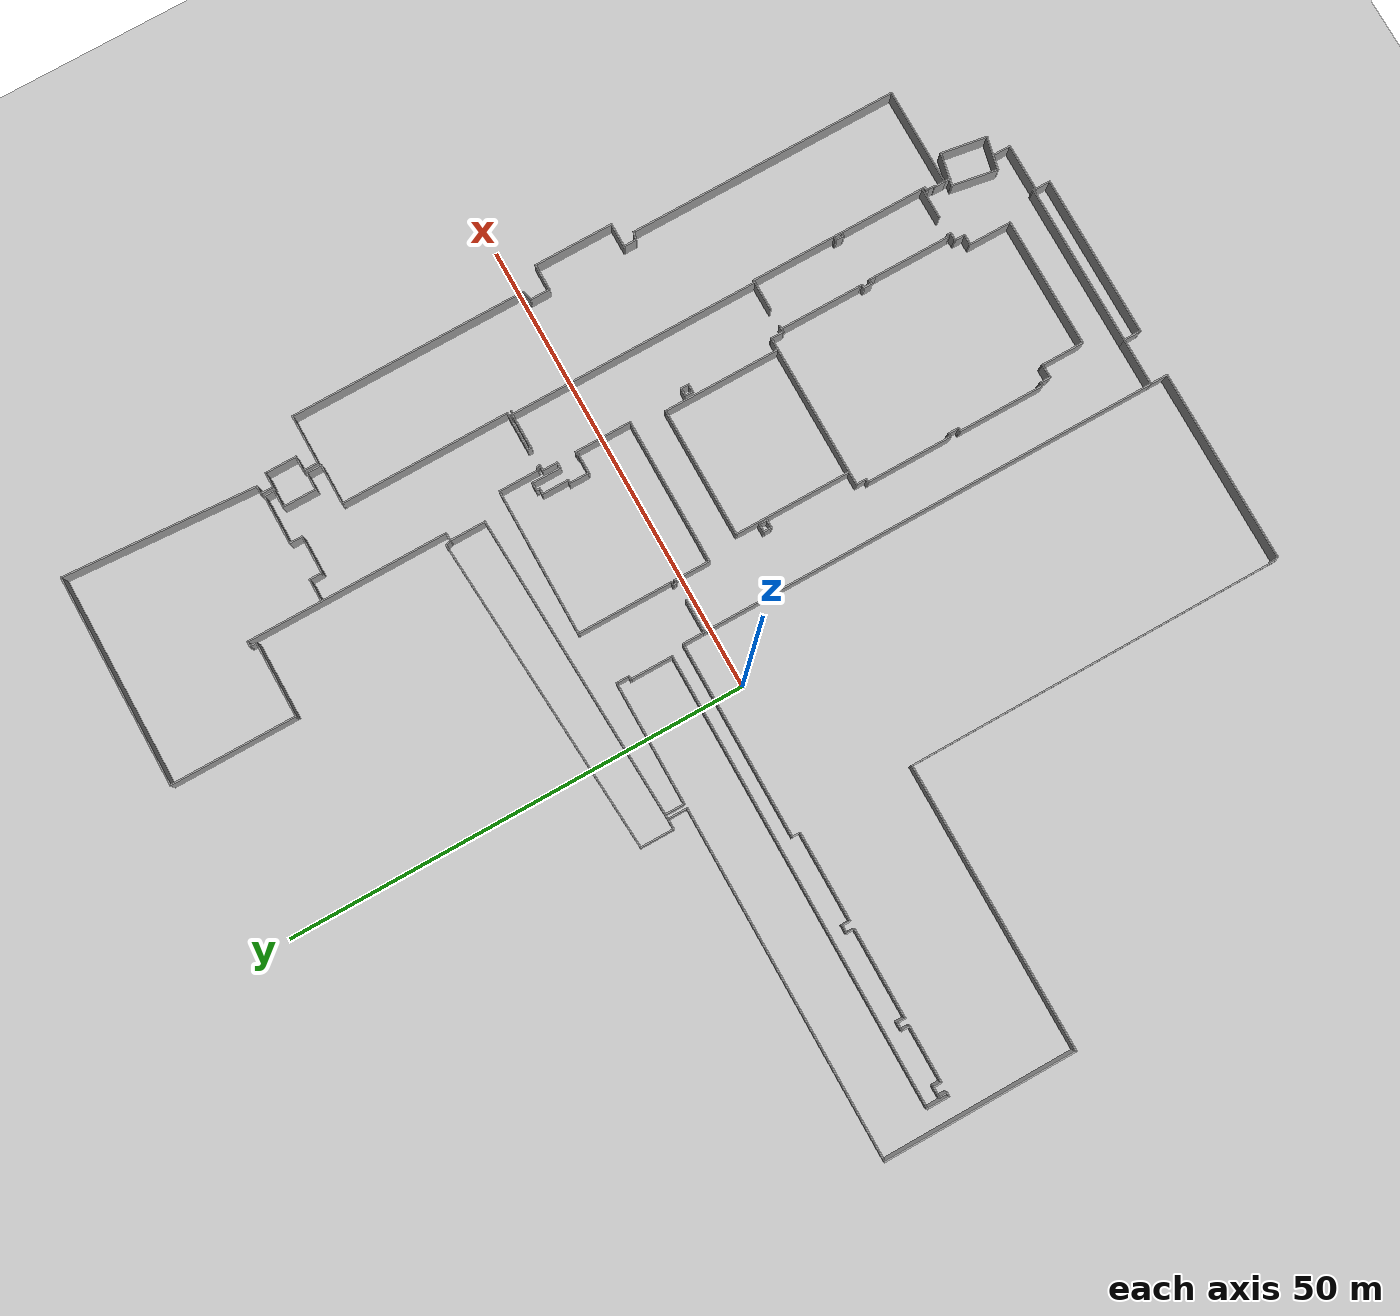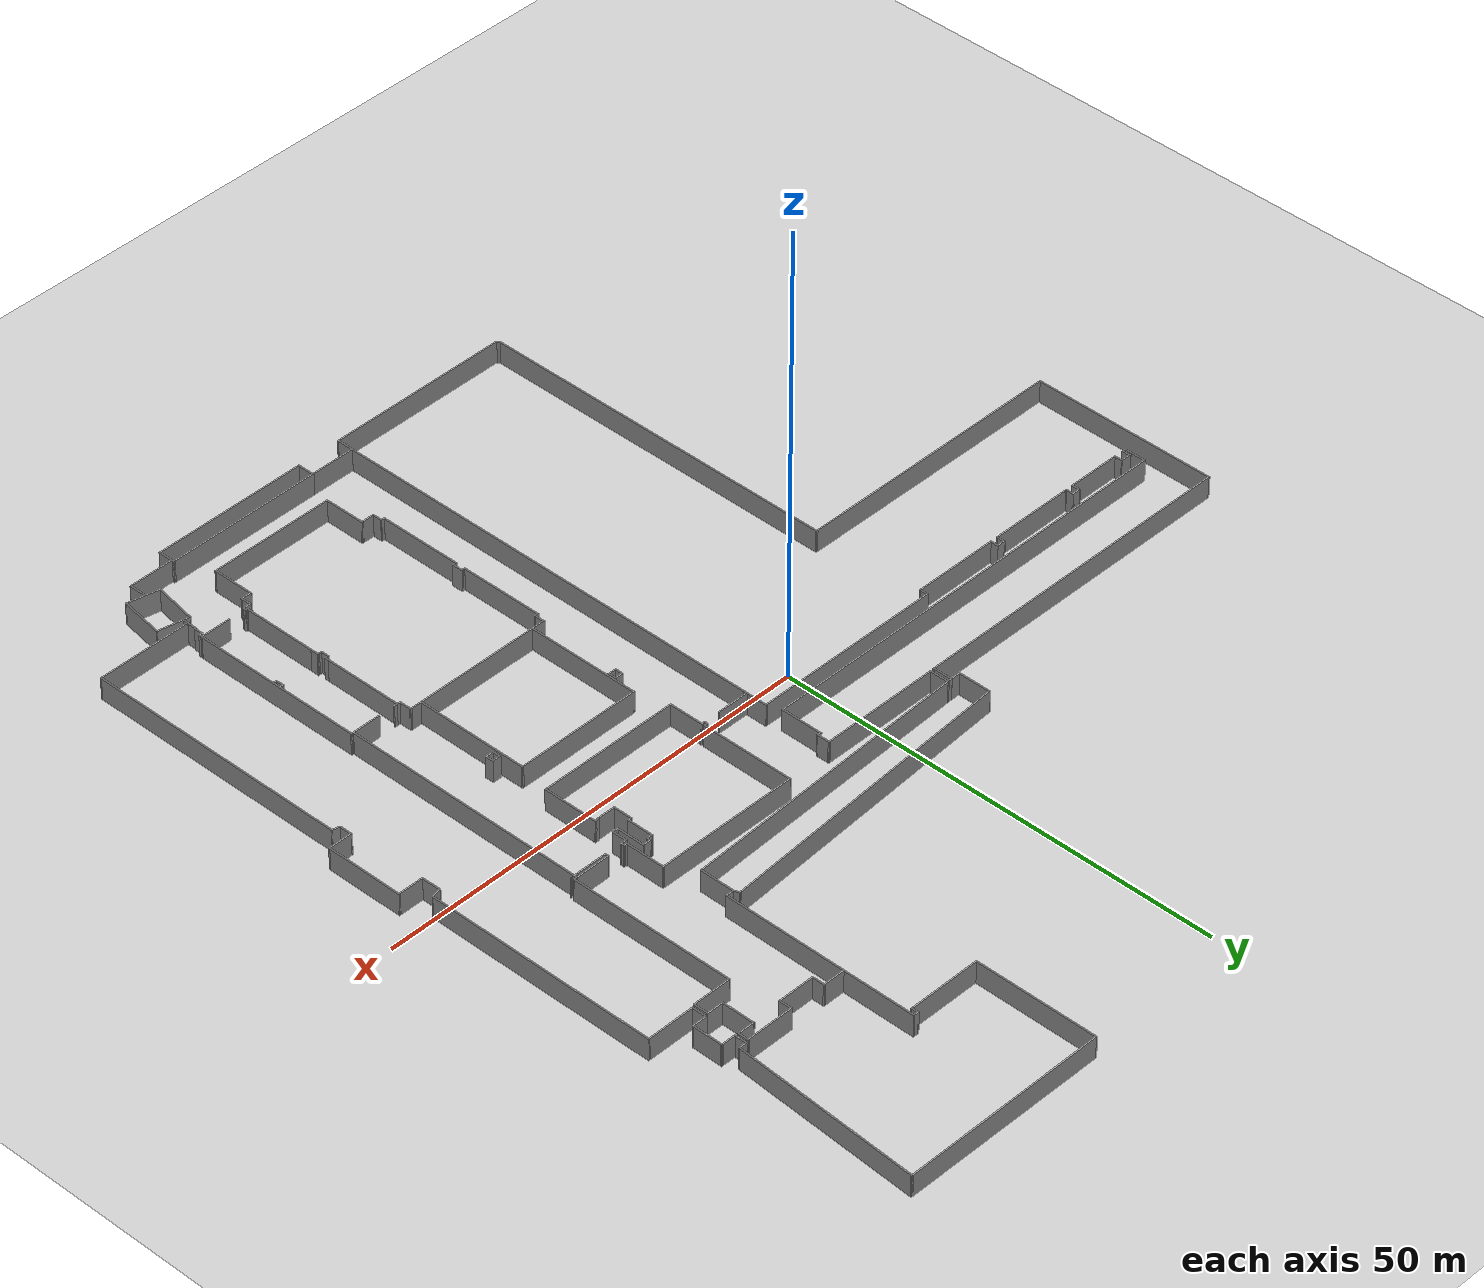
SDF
<sdf version="1.6">
 <world name="default">
  <light name="sun" type="directional">
   <pose>0 0 10 0 -0 0</pose>
   <diffuse>0.8 0.8 0.8 1</diffuse>
   <specular>0.2 0.2 0.2 1</specular>
   <attenuation>
    <range>1000</range>
    <constant>0.9</constant>
    <linear>0.01</linear>
    <quadratic>0.001</quadratic>
   </attenuation>
   <direction>-0.5 0.1 -0.9</direction>
  </light>
  <model name="ground_plane">
   <static>1</static>
   <link name="link">
    <collision name="collision">
     <geometry><plane><normal>0 0 1</normal><size>100 100</size></plane></geometry>
     <surface><friction><ode><mu>100</mu><mu2>50</mu2></ode></friction></surface>
    </collision>
    <visual name="visual">
     <cast_shadows>0</cast_shadows>
     <geometry><plane><normal>0 0 1</normal><size>100 100</size></plane></geometry>
     <material>
      <script><uri>file://media/materials/scripts/gazebo.material</uri><name>Gazebo/Grey</name></script>
     </material>
    </visual>
   </link>
  </model>
  <gravity>0 0 -9.8</gravity>
  <magnetic_field>6e-06 2.3e-05 -4.2e-05</magnetic_field>
  <atmosphere type="adiabatic"/>
  <physics name="default_physics" default="0" type="ode">
   <max_step_size>0.001</max_step_size>
   <real_time_factor>1</real_time_factor>
   <real_time_update_rate>1000</real_time_update_rate>
  </physics>
  <scene><ambient>0.4 0.4 0.4 1</ambient><background>0.7 0.7 0.7 1</background><shadows>1</shadows></scene>
  <spherical_coordinates>
   <surface_model>EARTH_WGS84</surface_model>
   <latitude_deg>0</latitude_deg>
   <longitude_deg>0</longitude_deg>
   <elevation>0</elevation>
   <heading_deg>0</heading_deg>
  </spherical_coordinates>
  <model name="SEH_double_doors_open">
   <pose>0.441181 0.582592 0 0 -0 0</pose>
   <link name="Wall_0">
    <collision name="Wall_0_Collision">
     <geometry><box><size>41 0.15 2.5</size></box></geometry>
     <pose>0 0 1.25 0 -0 0</pose>
    </collision>
    <visual name="Wall_0_Visual">
     <pose>0 0 1.25 0 -0 0</pose>
     <geometry><box><size>41 0.15 2.5</size></box></geometry>
     <material>
      <script><uri>file://media/materials/scripts/gazebo.material</uri><name>Gazebo/Grey</name></script>
      <ambient>1 1 1 1</ambient>
     </material>
     <meta><layer>0</layer></meta>
    </visual>
    <pose>-15.188 -31.31 0 0 -0 1.5708</pose>
   </link>
   <link name="Wall_1">
    <collision name="Wall_1_Collision">
     <geometry><box><size>31 0.15 2.5</size></box></geometry>
     <pose>0 0 1.25 0 -0 0</pose>
    </collision>
    <visual name="Wall_1_Visual">
     <pose>0 0 1.25 0 -0 0</pose>
     <geometry><box><size>31 0.15 2.5</size></box></geometry>
     <material>
      <script><uri>file://media/materials/scripts/gazebo.material</uri><name>Gazebo/Grey</name></script>
      <ambient>1 1 1 1</ambient>
     </material>
     <meta><layer>0</layer></meta>
    </visual>
    <pose>-30.613 -10.885 0 0 -0 3.14159</pose>
   </link>
   <link name="Wall_10">
    <collision name="Wall_10_Collision">
     <geometry><box><size>0.754811 0.15 2.5</size></box></geometry>
     <pose>0 0 1.25 0 -0 0</pose>
    </collision>
    <visual name="Wall_10_Visual">
     <pose>0 0 1.25 0 -0 0</pose>
     <geometry><box><size>0.754811 0.15 2.5</size></box></geometry>
     <material>
      <script><uri>file://media/materials/scripts/gazebo.material</uri><name>Gazebo/Grey</name></script>
      <ambient>1 1 1 1</ambient>
     </material>
     <meta><layer>0</layer></meta>
    </visual>
    <pose>25.6544 17.6654 0 0 -0 1.96559</pose>
   </link>
   <link name="Wall_101">
    <collision name="Wall_101_Collision">
     <geometry><box><size>19.75 0.15 2.5</size></box></geometry>
     <pose>0 0 1.25 0 -0 0</pose>
    </collision>
    <visual name="Wall_101_Visual">
     <pose>0 0 1.25 0 -0 0</pose>
     <geometry><box><size>19.75 0.15 2.5</size></box></geometry>
     <material>
      <script><uri>file://media/materials/scripts/gazebo.material</uri><name>Gazebo/Grey</name></script>
      <ambient>1 1 1 1</ambient>
     </material>
     <meta><layer>0</layer></meta>
    </visual>
    <pose>34.1091 -31.1312 0 0 -0 1.5708</pose>
   </link>
   <link name="Wall_103">
    <collision name="Wall_103_Collision">
     <geometry><box><size>3.5 0.15 2.5</size></box></geometry>
     <pose>0 0 1.25 0 -0 0</pose>
    </collision>
    <visual name="Wall_103_Visual">
     <pose>0 0 1.25 0 -0 0</pose>
     <geometry><box><size>3.5 0.15 2.5</size></box></geometry>
     <material>
      <script><uri>file://media/materials/scripts/gazebo.material</uri><name>Gazebo/Grey</name></script>
      <ambient>1 1 1 1</ambient>
     </material>
     <meta><layer>0</layer></meta>
    </visual>
    <pose>32.4341 -21.3312 0 0 -0 3.14159</pose>
   </link>
   <link name="Wall_105">
    <collision name="Wall_105_Collision">
     <geometry><box><size>0.5 0.15 2.5</size></box></geometry>
     <pose>0 0 1.25 0 -0 0</pose>
    </collision>
    <visual name="Wall_105_Visual">
     <pose>0 0 1.25 0 -0 0</pose>
     <geometry><box><size>0.5 0.15 2.5</size></box></geometry>
     <material>
      <script><uri>file://media/materials/scripts/gazebo.material</uri><name>Gazebo/Grey</name></script>
      <ambient>1 1 1 1</ambient>
     </material>
     <meta><layer>0</layer></meta>
    </visual>
    <pose>28.6395 -21.3021 0 0 -0 3.14159</pose>
   </link>
   <link name="Wall_106">
    <collision name="Wall_106_Collision">
     <geometry><box><size>9 0.15 2.5</size></box></geometry>
     <pose>0 0 1.25 0 -0 0</pose>
    </collision>
    <visual name="Wall_106_Visual">
     <pose>0 0 1.25 0 -0 0</pose>
     <geometry><box><size>9 0.15 2.5</size></box></geometry>
     <material>
      <script><uri>file://media/materials/scripts/gazebo.material</uri><name>Gazebo/Grey</name></script>
      <ambient>1 1 1 1</ambient>
     </material>
     <meta><layer>0</layer></meta>
    </visual>
    <pose>28.4645 -25.7271 0 0 0 -1.5708</pose>
   </link>
   <link name="Wall_109">
    <collision name="Wall_109_Collision">
     <geometry><box><size>0.5 0.15 2.5</size></box></geometry>
     <pose>0 0 1.25 0 -0 0</pose>
    </collision>
    <visual name="Wall_109_Visual">
     <pose>0 0 1.25 0 -0 0</pose>
     <geometry><box><size>0.5 0.15 2.5</size></box></geometry>
     <material>
      <script><uri>file://media/materials/scripts/gazebo.material</uri><name>Gazebo/Grey</name></script>
      <ambient>1 1 1 1</ambient>
     </material>
     <meta><layer>0</layer></meta>
    </visual>
    <pose>28.4645 -30.3271 0 0 0 -1.5708</pose>
   </link>
   <link name="Wall_110">
    <collision name="Wall_110_Collision">
     <geometry><box><size>0.5 0.15 2.5</size></box></geometry>
     <pose>0 0 1.25 0 -0 0</pose>
    </collision>
    <visual name="Wall_110_Visual">
     <pose>0 0 1.25 0 -0 0</pose>
     <geometry><box><size>0.5 0.15 2.5</size></box></geometry>
     <material>
      <script><uri>file://media/materials/scripts/gazebo.material</uri><name>Gazebo/Grey</name></script>
      <ambient>1 1 1 1</ambient>
     </material>
     <meta><layer>0</layer></meta>
    </visual>
    <pose>28.2895 -30.5021 0 0 -0 3.14159</pose>
   </link>
   <link name="Wall_111">
    <collision name="Wall_111_Collision">
     <geometry><box><size>1 0.15 2.5</size></box></geometry>
     <pose>0 0 1.25 0 -0 0</pose>
    </collision>
    <visual name="Wall_111_Visual">
     <pose>0 0 1.25 0 -0 0</pose>
     <geometry><box><size>1 0.15 2.5</size></box></geometry>
     <material>
      <script><uri>file://media/materials/scripts/gazebo.material</uri><name>Gazebo/Grey</name></script>
      <ambient>1 1 1 1</ambient>
     </material>
     <meta><layer>0</layer></meta>
    </visual>
    <pose>28.1145 -30.9271 0 0 0 -1.5708</pose>
   </link>
   <link name="Wall_112">
    <collision name="Wall_112_Collision">
     <geometry><box><size>0.5 0.15 2.5</size></box></geometry>
     <pose>0 0 1.25 0 -0 0</pose>
    </collision>
    <visual name="Wall_112_Visual">
     <pose>0 0 1.25 0 -0 0</pose>
     <geometry><box><size>0.5 0.15 2.5</size></box></geometry>
     <material>
      <script><uri>file://media/materials/scripts/gazebo.material</uri><name>Gazebo/Grey</name></script>
      <ambient>1 1 1 1</ambient>
     </material>
     <meta><layer>0</layer></meta>
    </visual>
    <pose>28.2895 -31.3521 0 0 -0 0</pose>
   </link>
   <link name="Wall_113">
    <collision name="Wall_113_Collision">
     <geometry><box><size>0.25 0.15 2.5</size></box></geometry>
     <pose>0 0 1.25 0 -0 0</pose>
    </collision>
    <visual name="Wall_113_Visual">
     <pose>0 0 1.25 0 -0 0</pose>
     <geometry><box><size>0.25 0.15 2.5</size></box></geometry>
     <material>
      <script><uri>file://media/materials/scripts/gazebo.material</uri><name>Gazebo/Grey</name></script>
      <ambient>1 1 1 1</ambient>
     </material>
     <meta><layer>0</layer></meta>
    </visual>
    <pose>28.5145 -31.3521 0 0 -0 0</pose>
   </link>
   <link name="Wall_114">
    <collision name="Wall_114_Collision">
     <geometry><box><size>0.931161 0.15 2.5</size></box></geometry>
     <pose>0 0 1.25 0 -0 0</pose>
    </collision>
    <visual name="Wall_114_Visual">
     <pose>0 0 1.25 0 -0 0</pose>
     <geometry><box><size>0.931161 0.15 2.5</size></box></geometry>
     <material>
      <script><uri>file://media/materials/scripts/gazebo.material</uri><name>Gazebo/Grey</name></script>
      <ambient>1 1 1 1</ambient>
     </material>
     <meta><layer>0</layer></meta>
    </visual>
    <pose>28.5648 -31.7427 0 0 0 -1.56992</pose>
   </link>
   <link name="Wall_116">
    <collision name="Wall_116_Collision">
     <geometry><box><size>0.5 0.15 2.5</size></box></geometry>
     <pose>0 0 1.25 0 -0 0</pose>
    </collision>
    <visual name="Wall_116_Visual">
     <pose>0 0 1.25 0 -0 0</pose>
     <geometry><box><size>0.5 0.15 2.5</size></box></geometry>
     <material>
      <script><uri>file://media/materials/scripts/gazebo.material</uri><name>Gazebo/Grey</name></script>
      <ambient>1 1 1 1</ambient>
     </material>
     <meta><layer>0</layer></meta>
    </visual>
    <pose>33.8845 -30.5093 0 0 -0 3.14159</pose>
   </link>
   <link name="Wall_117">
    <collision name="Wall_117_Collision">
     <geometry><box><size>1 0.15 2.5</size></box></geometry>
     <pose>0 0 1.25 0 -0 0</pose>
    </collision>
    <visual name="Wall_117_Visual">
     <pose>0 0 1.25 0 -0 0</pose>
     <geometry><box><size>1 0.15 2.5</size></box></geometry>
     <material>
      <script><uri>file://media/materials/scripts/gazebo.material</uri><name>Gazebo/Grey</name></script>
      <ambient>1 1 1 1</ambient>
     </material>
     <meta><layer>0</layer></meta>
    </visual>
    <pose>33.7095 -30.9343 0 0 0 -1.5708</pose>
   </link>
   <link name="Wall_118">
    <collision name="Wall_118_Collision">
     <geometry><box><size>0.5 0.15 2.5</size></box></geometry>
     <pose>0 0 1.25 0 -0 0</pose>
    </collision>
    <visual name="Wall_118_Visual">
     <pose>0 0 1.25 0 -0 0</pose>
     <geometry><box><size>0.5 0.15 2.5</size></box></geometry>
     <material>
      <script><uri>file://media/materials/scripts/gazebo.material</uri><name>Gazebo/Grey</name></script>
      <ambient>1 1 1 1</ambient>
     </material>
     <meta><layer>0</layer></meta>
    </visual>
    <pose>33.8845 -31.3593 0 0 -0 0</pose>
   </link>
   <link name="Wall_12">
    <collision name="Wall_12_Collision">
     <geometry><box><size>1 0.15 2.5</size></box></geometry>
     <pose>0 0 1.25 0 -0 0</pose>
    </collision>
    <visual name="Wall_12_Visual">
     <pose>0 0 1.25 0 -0 0</pose>
     <geometry><box><size>1 0.15 2.5</size></box></geometry>
     <material>
      <script><uri>file://media/materials/scripts/gazebo.material</uri><name>Gazebo/Grey</name></script>
      <ambient>1 1 1 1</ambient>
     </material>
     <meta><layer>0</layer></meta>
    </visual>
    <pose>26.1957 17.3863 0 0 -0 0</pose>
   </link>
   <link name="Wall_120">
    <collision name="Wall_120_Collision">
     <geometry><box><size>50.25 0.15 2.5</size></box></geometry>
     <pose>0 0 1.25 0 -0 0</pose>
    </collision>
    <visual name="Wall_120_Visual">
     <pose>0 0 1.25 0 -0 0</pose>
     <geometry><box><size>50.25 0.15 2.5</size></box></geometry>
     <material>
      <script><uri>file://media/materials/scripts/gazebo.material</uri><name>Gazebo/Grey</name></script>
      <ambient>1 1 1 1</ambient>
     </material>
     <meta><layer>0</layer></meta>
    </visual>
    <pose>5.8537 -25.2205 0 0 -0 1.5708</pose>
   </link>
   <link name="Wall_122">
    <collision name="Wall_122_Collision">
     <geometry><box><size>0.5 0.15 2.5</size></box></geometry>
     <pose>0 0 1.25 0 -0 0</pose>
    </collision>
    <visual name="Wall_122_Visual">
     <pose>0 0 1.25 0 -0 0</pose>
     <geometry><box><size>0.5 0.15 2.5</size></box></geometry>
     <material>
      <script><uri>file://media/materials/scripts/gazebo.material</uri><name>Gazebo/Grey</name></script>
      <ambient>1 1 1 1</ambient>
     </material>
     <meta><layer>0</layer></meta>
    </visual>
    <pose>5.8537 0.004461 0 0 -0 1.5708</pose>
   </link>
   <link name="Wall_123">
    <collision name="Wall_123_Collision">
     <geometry><box><size>3.75 0.15 2.5</size></box></geometry>
     <pose>0 0 1.25 0 -0 0</pose>
    </collision>
    <visual name="Wall_123_Visual">
     <pose>0 0 1.25 0 -0 0</pose>
     <geometry><box><size>3.75 0.15 2.5</size></box></geometry>
     <material>
      <script><uri>file://media/materials/scripts/gazebo.material</uri><name>Gazebo/Grey</name></script>
      <ambient>1 1 1 1</ambient>
     </material>
     <meta><layer>0</layer></meta>
    </visual>
    <pose>7.6537 0.179461 0 0 -0 0</pose>
   </link>
   <link name="Wall_125">
    <collision name="Wall_125_Collision">
     <geometry><box><size>0.5 0.15 2.5</size></box></geometry>
     <pose>0 0 1.25 0 -0 0</pose>
    </collision>
    <visual name="Wall_125_Visual">
     <pose>0 0 1.25 0 -0 0</pose>
     <geometry><box><size>0.5 0.15 2.5</size></box></geometry>
     <material>
      <script><uri>file://media/materials/scripts/gazebo.material</uri><name>Gazebo/Grey</name></script>
      <ambient>1 1 1 1</ambient>
     </material>
     <meta><layer>0</layer></meta>
    </visual>
    <pose>11.5048 0.195336 0 0 -0 0</pose>
   </link>
   <link name="Wall_126">
    <collision name="Wall_126_Collision">
     <geometry><box><size>4 0.15 2.5</size></box></geometry>
     <pose>0 0 1.25 0 -0 0</pose>
    </collision>
    <visual name="Wall_126_Visual">
     <pose>0 0 1.25 0 -0 0</pose>
     <geometry><box><size>4 0.15 2.5</size></box></geometry>
     <material>
      <script><uri>file://media/materials/scripts/gazebo.material</uri><name>Gazebo/Grey</name></script>
      <ambient>1 1 1 1</ambient>
     </material>
     <meta><layer>0</layer></meta>
    </visual>
    <pose>11.6798 -1.72966 0 0 0 -1.5708</pose>
   </link>
   <link name="Wall_127">
    <collision name="Wall_127_Collision">
     <geometry><box><size>16 0.15 2.5</size></box></geometry>
     <pose>0 0 1.25 0 -0 0</pose>
    </collision>
    <visual name="Wall_127_Visual">
     <pose>0 0 1.25 0 -0 0</pose>
     <geometry><box><size>16 0.15 2.5</size></box></geometry>
     <material>
      <script><uri>file://media/materials/scripts/gazebo.material</uri><name>Gazebo/Grey</name></script>
      <ambient>1 1 1 1</ambient>
     </material>
     <meta><layer>0</layer></meta>
    </visual>
    <pose>19.6048 -3.65466 0 0 -0 0</pose>
   </link>
   <link name="Wall_128">
    <collision name="Wall_128_Collision">
     <geometry><box><size>6.25 0.15 2.5</size></box></geometry>
     <pose>0 0 1.25 0 -0 0</pose>
    </collision>
    <visual name="Wall_128_Visual">
     <pose>0 0 1.25 0 -0 0</pose>
     <geometry><box><size>6.25 0.15 2.5</size></box></geometry>
     <material>
      <script><uri>file://media/materials/scripts/gazebo.material</uri><name>Gazebo/Grey</name></script>
      <ambient>1 1 1 1</ambient>
     </material>
     <meta><layer>0</layer></meta>
    </visual>
    <pose>27.5298 -0.604664 0 0 -0 1.5708</pose>
   </link>
   <link name="Wall_129">
    <collision name="Wall_129_Collision">
     <geometry><box><size>0.5 0.15 2.5</size></box></geometry>
     <pose>0 0 1.25 0 -0 0</pose>
    </collision>
    <visual name="Wall_129_Visual">
     <pose>0 0 1.25 0 -0 0</pose>
     <geometry><box><size>0.5 0.15 2.5</size></box></geometry>
     <material>
      <script><uri>file://media/materials/scripts/gazebo.material</uri><name>Gazebo/Grey</name></script>
      <ambient>1 1 1 1</ambient>
     </material>
     <meta><layer>0</layer></meta>
    </visual>
    <pose>27.3548 2.44534 0 0 -0 3.14159</pose>
   </link>
   <link name="Wall_13">
    <collision name="Wall_13_Collision">
     <geometry><box><size>22 0.15 2.5</size></box></geometry>
     <pose>0 0 1.25 0 -0 0</pose>
    </collision>
    <visual name="Wall_13_Visual">
     <pose>0 0 1.25 0 -0 0</pose>
     <geometry><box><size>22 0.15 2.5</size></box></geometry>
     <material>
      <script><uri>file://media/materials/scripts/gazebo.material</uri><name>Gazebo/Grey</name></script>
      <ambient>1 1 1 1</ambient>
     </material>
     <meta><layer>0</layer></meta>
    </visual>
    <pose>26.6207 28.3113 0 0 -0 1.5708</pose>
   </link>
   <link name="Wall_133">
    <collision name="Wall_133_Collision">
     <geometry><box><size>0.25 0.15 2.5</size></box></geometry>
     <pose>0 0 1.25 0 -0 0</pose>
    </collision>
    <visual name="Wall_133_Visual">
     <pose>0 0 1.25 0 -0 0</pose>
     <geometry><box><size>0.25 0.15 2.5</size></box></geometry>
     <material>
      <script><uri>file://media/materials/scripts/gazebo.material</uri><name>Gazebo/Grey</name></script>
      <ambient>1 1 1 1</ambient>
     </material>
     <meta><layer>0</layer></meta>
    </visual>
    <pose>27.1798 2.39534 0 0 0 -1.5708</pose>
   </link>
   <link name="Wall_134">
    <collision name="Wall_134_Collision">
     <geometry><box><size>2.25 0.15 2.5</size></box></geometry>
     <pose>0 0 1.25 0 -0 0</pose>
    </collision>
    <visual name="Wall_134_Visual">
     <pose>0 0 1.25 0 -0 0</pose>
     <geometry><box><size>2.25 0.15 2.5</size></box></geometry>
     <material>
      <script><uri>file://media/materials/scripts/gazebo.material</uri><name>Gazebo/Grey</name></script>
      <ambient>1 1 1 1</ambient>
     </material>
     <meta><layer>0</layer></meta>
    </visual>
    <pose>26.1298 2.34534 0 0 -0 3.14159</pose>
   </link>
   <link name="Wall_135">
    <collision name="Wall_135_Collision">
     <geometry><box><size>2.25 0.15 2.5</size></box></geometry>
     <pose>0 0 1.25 0 -0 0</pose>
    </collision>
    <visual name="Wall_135_Visual">
     <pose>0 0 1.25 0 -0 0</pose>
     <geometry><box><size>2.25 0.15 2.5</size></box></geometry>
     <material>
      <script><uri>file://media/materials/scripts/gazebo.material</uri><name>Gazebo/Grey</name></script>
      <ambient>1 1 1 1</ambient>
     </material>
     <meta><layer>0</layer></meta>
    </visual>
    <pose>25.0798 3.39534 0 0 -0 1.5708</pose>
   </link>
   <link name="Wall_136">
    <collision name="Wall_136_Collision">
     <geometry><box><size>0.5 0.15 2.5</size></box></geometry>
     <pose>0 0 1.25 0 -0 0</pose>
    </collision>
    <visual name="Wall_136_Visual">
     <pose>0 0 1.25 0 -0 0</pose>
     <geometry><box><size>0.5 0.15 2.5</size></box></geometry>
     <material>
      <script><uri>file://media/materials/scripts/gazebo.material</uri><name>Gazebo/Grey</name></script>
      <ambient>1 1 1 1</ambient>
     </material>
     <meta><layer>0</layer></meta>
    </visual>
    <pose>25.2548 4.44534 0 0 -0 0</pose>
   </link>
   <link name="Wall_137">
    <collision name="Wall_137_Collision">
     <geometry><box><size>3 0.15 2.5</size></box></geometry>
     <pose>0 0 1.25 0 -0 0</pose>
    </collision>
    <visual name="Wall_137_Visual">
     <pose>0 0 1.25 0 -0 0</pose>
     <geometry><box><size>3 0.15 2.5</size></box></geometry>
     <material>
      <script><uri>file://media/materials/scripts/gazebo.material</uri><name>Gazebo/Grey</name></script>
      <ambient>1 1 1 1</ambient>
     </material>
     <meta><layer>0</layer></meta>
    </visual>
    <pose>25.4298 5.87034 0 0 -0 1.5708</pose>
   </link>
   <link name="Wall_138">
    <collision name="Wall_138_Collision">
     <geometry><box><size>0.75 0.15 2.5</size></box></geometry>
     <pose>0 0 1.25 0 -0 0</pose>
    </collision>
    <visual name="Wall_138_Visual">
     <pose>0 0 1.25 0 -0 0</pose>
     <geometry><box><size>0.75 0.15 2.5</size></box></geometry>
     <material>
      <script><uri>file://media/materials/scripts/gazebo.material</uri><name>Gazebo/Grey</name></script>
      <ambient>1 1 1 1</ambient>
     </material>
     <meta><layer>0</layer></meta>
    </visual>
    <pose>25.7298 7.29534 0 0 -0 0</pose>
   </link>
   <link name="Wall_143">
    <collision name="Wall_143_Collision">
     <geometry><box><size>0.5 0.15 2.5</size></box></geometry>
     <pose>0 0 1.25 0 -0 0</pose>
    </collision>
    <visual name="Wall_143_Visual">
     <pose>0 0 1.25 0 -0 0</pose>
     <geometry><box><size>0.5 0.15 2.5</size></box></geometry>
     <material>
      <script><uri>file://media/materials/scripts/gazebo.material</uri><name>Gazebo/Grey</name></script>
      <ambient>1 1 1 1</ambient>
     </material>
     <meta><layer>0</layer></meta>
    </visual>
    <pose>26.0298 7.47034 0 0 -0 1.5708</pose>
   </link>
   <link name="Wall_144">
    <collision name="Wall_144_Collision">
     <geometry><box><size>1 0.15 2.5</size></box></geometry>
     <pose>0 0 1.25 0 -0 0</pose>
    </collision>
    <visual name="Wall_144_Visual">
     <pose>0 0 1.25 0 -0 0</pose>
     <geometry><box><size>1 0.15 2.5</size></box></geometry>
     <material>
      <script><uri>file://media/materials/scripts/gazebo.material</uri><name>Gazebo/Grey</name></script>
      <ambient>1 1 1 1</ambient>
     </material>
     <meta><layer>0</layer></meta>
    </visual>
    <pose>26.4548 7.64534 0 0 -0 0</pose>
   </link>
   <link name="Wall_145">
    <collision name="Wall_145_Collision">
     <geometry><box><size>3.25 0.15 2.5</size></box></geometry>
     <pose>0 0 1.25 0 -0 0</pose>
    </collision>
    <visual name="Wall_145_Visual">
     <pose>0 0 1.25 0 -0 0</pose>
     <geometry><box><size>3.25 0.15 2.5</size></box></geometry>
     <material>
      <script><uri>file://media/materials/scripts/gazebo.material</uri><name>Gazebo/Grey</name></script>
      <ambient>1 1 1 1</ambient>
     </material>
     <meta><layer>0</layer></meta>
    </visual>
    <pose>26.8798 6.09534 0 0 0 -1.5708</pose>
   </link>
   <link name="Wall_146">
    <collision name="Wall_146_Collision">
     <geometry><box><size>0.75 0.15 2.5</size></box></geometry>
     <pose>0 0 1.25 0 -0 0</pose>
    </collision>
    <visual name="Wall_146_Visual">
     <pose>0 0 1.25 0 -0 0</pose>
     <geometry><box><size>0.75 0.15 2.5</size></box></geometry>
     <material>
      <script><uri>file://media/materials/scripts/gazebo.material</uri><name>Gazebo/Grey</name></script>
      <ambient>1 1 1 1</ambient>
     </material>
     <meta><layer>0</layer></meta>
    </visual>
    <pose>27.1798 4.54534 0 0 -0 0</pose>
   </link>
   <link name="Wall_147">
    <collision name="Wall_147_Collision">
     <geometry><box><size>1.75 0.15 2.5</size></box></geometry>
     <pose>0 0 1.25 0 -0 0</pose>
    </collision>
    <visual name="Wall_147_Visual">
     <pose>0 0 1.25 0 -0 0</pose>
     <geometry><box><size>1.75 0.15 2.5</size></box></geometry>
     <material>
      <script><uri>file://media/materials/scripts/gazebo.material</uri><name>Gazebo/Grey</name></script>
      <ambient>1 1 1 1</ambient>
     </material>
     <meta><layer>0</layer></meta>
    </visual>
    <pose>27.4798 5.34534 0 0 -0 1.5708</pose>
   </link>
   <link name="Wall_148">
    <collision name="Wall_148_Collision">
     <geometry><box><size>0.75 0.15 2.5</size></box></geometry>
     <pose>0 0 1.25 0 -0 0</pose>
    </collision>
    <visual name="Wall_148_Visual">
     <pose>0 0 1.25 0 -0 0</pose>
     <geometry><box><size>0.75 0.15 2.5</size></box></geometry>
     <material>
      <script><uri>file://media/materials/scripts/gazebo.material</uri><name>Gazebo/Grey</name></script>
      <ambient>1 1 1 1</ambient>
     </material>
     <meta><layer>0</layer></meta>
    </visual>
    <pose>27.7798 6.14534 0 0 -0 0</pose>
   </link>
   <link name="Wall_150">
    <collision name="Wall_150_Collision">
     <geometry><box><size>4 0.15 2.5</size></box></geometry>
     <pose>0 0 1.25 0 -0 0</pose>
    </collision>
    <visual name="Wall_150_Visual">
     <pose>0 0 1.25 0 -0 0</pose>
     <geometry><box><size>4 0.15 2.5</size></box></geometry>
     <material>
      <script><uri>file://media/materials/scripts/gazebo.material</uri><name>Gazebo/Grey</name></script>
      <ambient>1 1 1 1</ambient>
     </material>
     <meta><layer>0</layer></meta>
    </visual>
    <pose>31.9514 6.07094 0 0 -0 0</pose>
   </link>
   <link name="Wall_151">
    <collision name="Wall_151_Collision">
     <geometry><box><size>27.5 0.15 2.5</size></box></geometry>
     <pose>0 0 1.25 0 -0 0</pose>
    </collision>
    <visual name="Wall_151_Visual">
     <pose>0 0 1.25 0 -0 0</pose>
     <geometry><box><size>27.5 0.15 2.5</size></box></geometry>
     <material>
      <script><uri>file://media/materials/scripts/gazebo.material</uri><name>Gazebo/Grey</name></script>
      <ambient>1 1 1 1</ambient>
     </material>
     <meta><layer>0</layer></meta>
    </visual>
    <pose>33.8764 -7.60406 0 0 0 -1.5708</pose>
   </link>
   <link name="Wall_156">
    <collision name="Wall_156_Collision">
     <geometry><box><size>0.5 0.15 2.5</size></box></geometry>
     <pose>0 0 1.25 0 -0 0</pose>
    </collision>
    <visual name="Wall_156_Visual">
     <pose>0 0 1.25 0 -0 0</pose>
     <geometry><box><size>0.5 0.15 2.5</size></box></geometry>
     <material>
      <script><uri>file://media/materials/scripts/gazebo.material</uri><name>Gazebo/Grey</name></script>
      <ambient>1 1 1 1</ambient>
     </material>
     <meta><layer>0</layer></meta>
    </visual>
    <pose>28.2895 -21.3021 0 0 -0 3.14159</pose>
   </link>
   <link name="Wall_157">
    <collision name="Wall_157_Collision">
     <geometry><box><size>1.5 0.15 2.5</size></box></geometry>
     <pose>0 0 1.25 0 -0 0</pose>
    </collision>
    <visual name="Wall_157_Visual">
     <pose>0 0 1.25 0 -0 0</pose>
     <geometry><box><size>1.5 0.15 2.5</size></box></geometry>
     <material>
      <script><uri>file://media/materials/scripts/gazebo.material</uri><name>Gazebo/Grey</name></script>
      <ambient>1 1 1 1</ambient>
     </material>
     <meta><layer>0</layer></meta>
    </visual>
    <pose>28.1145 -20.6271 0 0 -0 1.5708</pose>
   </link>
   <link name="Wall_158">
    <collision name="Wall_158_Collision">
     <geometry><box><size>17 0.15 2.5</size></box></geometry>
     <pose>0 0 1.25 0 -0 0</pose>
    </collision>
    <visual name="Wall_158_Visual">
     <pose>0 0 1.25 0 -0 0</pose>
     <geometry><box><size>17 0.15 2.5</size></box></geometry>
     <material>
      <script><uri>file://media/materials/scripts/gazebo.material</uri><name>Gazebo/Grey</name></script>
      <ambient>1 1 1 1</ambient>
     </material>
     <meta><layer>0</layer></meta>
    </visual>
    <pose>19.6895 -19.9521 0 0 -0 3.14159</pose>
   </link>
   <link name="Wall_159">
    <collision name="Wall_159_Collision">
     <geometry><box><size>1.25 0.15 2.5</size></box></geometry>
     <pose>0 0 1.25 0 -0 0</pose>
    </collision>
    <visual name="Wall_159_Visual">
     <pose>0 0 1.25 0 -0 0</pose>
     <geometry><box><size>1.25 0.15 2.5</size></box></geometry>
     <material>
      <script><uri>file://media/materials/scripts/gazebo.material</uri><name>Gazebo/Grey</name></script>
      <ambient>1 1 1 1</ambient>
     </material>
     <meta><layer>0</layer></meta>
    </visual>
    <pose>11.2645 -20.5021 0 0 0 -1.5708</pose>
   </link>
   <link name="Wall_160">
    <collision name="Wall_160_Collision">
     <geometry><box><size>0.5 0.15 2.5</size></box></geometry>
     <pose>0 0 1.25 0 -0 0</pose>
    </collision>
    <visual name="Wall_160_Visual">
     <pose>0 0 1.25 0 -0 0</pose>
     <geometry><box><size>0.5 0.15 2.5</size></box></geometry>
     <material>
      <script><uri>file://media/materials/scripts/gazebo.material</uri><name>Gazebo/Grey</name></script>
      <ambient>1 1 1 1</ambient>
     </material>
     <meta><layer>0</layer></meta>
    </visual>
    <pose>11.0895 -21.0521 0 0 -0 3.14159</pose>
   </link>
   <link name="Wall_161">
    <collision name="Wall_161_Collision">
     <geometry><box><size>9.5 0.15 2.5</size></box></geometry>
     <pose>0 0 1.25 0 -0 0</pose>
    </collision>
    <visual name="Wall_161_Visual">
     <pose>0 0 1.25 0 -0 0</pose>
     <geometry><box><size>9.5 0.15 2.5</size></box></geometry>
     <material>
      <script><uri>file://media/materials/scripts/gazebo.material</uri><name>Gazebo/Grey</name></script>
      <ambient>1 1 1 1</ambient>
     </material>
     <meta><layer>0</layer></meta>
    </visual>
    <pose>10.9145 -25.7271 0 0 0 -1.5708</pose>
   </link>
   <link name="Wall_163">
    <collision name="Wall_163_Collision">
     <geometry><box><size>0.5 0.15 2.5</size></box></geometry>
     <pose>0 0 1.25 0 -0 0</pose>
    </collision>
    <visual name="Wall_163_Visual">
     <pose>0 0 1.25 0 -0 0</pose>
     <geometry><box><size>0.5 0.15 2.5</size></box></geometry>
     <material>
      <script><uri>file://media/materials/scripts/gazebo.material</uri><name>Gazebo/Grey</name></script>
      <ambient>1 1 1 1</ambient>
     </material>
     <meta><layer>0</layer></meta>
    </visual>
    <pose>11.0895 -30.4021 0 0 -0 0</pose>
   </link>
   <link name="Wall_164">
    <collision name="Wall_164_Collision">
     <geometry><box><size>1.25 0.15 2.5</size></box></geometry>
     <pose>0 0 1.25 0 -0 0</pose>
    </collision>
    <visual name="Wall_164_Visual">
     <pose>0 0 1.25 0 -0 0</pose>
     <geometry><box><size>1.25 0.15 2.5</size></box></geometry>
     <material>
      <script><uri>file://media/materials/scripts/gazebo.material</uri><name>Gazebo/Grey</name></script>
      <ambient>1 1 1 1</ambient>
     </material>
     <meta><layer>0</layer></meta>
    </visual>
    <pose>11.2645 -30.9521 0 0 0 -1.5708</pose>
   </link>
   <link name="Wall_165">
    <collision name="Wall_165_Collision">
     <geometry><box><size>0.5 0.15 2.5</size></box></geometry>
     <pose>0 0 1.25 0 -0 0</pose>
    </collision>
    <visual name="Wall_165_Visual">
     <pose>0 0 1.25 0 -0 0</pose>
     <geometry><box><size>0.5 0.15 2.5</size></box></geometry>
     <material>
      <script><uri>file://media/materials/scripts/gazebo.material</uri><name>Gazebo/Grey</name></script>
      <ambient>1 1 1 1</ambient>
     </material>
     <meta><layer>0</layer></meta>
    </visual>
    <pose>11.0895 -31.5021 0 0 -0 3.14159</pose>
   </link>
   <link name="Wall_166">
    <collision name="Wall_166_Collision">
     <geometry><box><size>9.5 0.15 2.5</size></box></geometry>
     <pose>0 0 1.25 0 -0 0</pose>
    </collision>
    <visual name="Wall_166_Visual">
     <pose>0 0 1.25 0 -0 0</pose>
     <geometry><box><size>9.5 0.15 2.5</size></box></geometry>
     <material>
      <script><uri>file://media/materials/scripts/gazebo.material</uri><name>Gazebo/Grey</name></script>
      <ambient>1 1 1 1</ambient>
     </material>
     <meta><layer>0</layer></meta>
    </visual>
    <pose>10.9145 -36.1771 0 0 0 -1.5708</pose>
   </link>
   <link name="Wall_167">
    <collision name="Wall_167_Collision">
     <geometry><box><size>0.5 0.15 2.5</size></box></geometry>
     <pose>0 0 1.25 0 -0 0</pose>
    </collision>
    <visual name="Wall_167_Visual">
     <pose>0 0 1.25 0 -0 0</pose>
     <geometry><box><size>0.5 0.15 2.5</size></box></geometry>
     <material>
      <script><uri>file://media/materials/scripts/gazebo.material</uri><name>Gazebo/Grey</name></script>
      <ambient>1 1 1 1</ambient>
     </material>
     <meta><layer>0</layer></meta>
    </visual>
    <pose>11.0895 -40.8521 0 0 -0 0</pose>
   </link>
   <link name="Wall_168">
    <collision name="Wall_168_Collision">
     <geometry><box><size>1.25 0.15 2.5</size></box></geometry>
     <pose>0 0 1.25 0 -0 0</pose>
    </collision>
    <visual name="Wall_168_Visual">
     <pose>0 0 1.25 0 -0 0</pose>
     <geometry><box><size>1.25 0.15 2.5</size></box></geometry>
     <material>
      <script><uri>file://media/materials/scripts/gazebo.material</uri><name>Gazebo/Grey</name></script>
      <ambient>1 1 1 1</ambient>
     </material>
     <meta><layer>0</layer></meta>
    </visual>
    <pose>11.2645 -41.4021 0 0 0 -1.5708</pose>
   </link>
   <link name="Wall_169">
    <collision name="Wall_169_Collision">
     <geometry><box><size>1.60081 0.15 2.5</size></box></geometry>
     <pose>0 0 1.25 0 -0 0</pose>
    </collision>
    <visual name="Wall_169_Visual">
     <pose>0 0 1.25 0 -0 0</pose>
     <geometry><box><size>1.60081 0.15 2.5</size></box></geometry>
     <material>
      <script><uri>file://media/materials/scripts/gazebo.material</uri><name>Gazebo/Grey</name></script>
      <ambient>1 1 1 1</ambient>
     </material>
     <meta><layer>0</layer></meta>
    </visual>
    <pose>11.9898 -41.9427 0 0 -0 0.012986</pose>
   </link>
   <link name="Wall_17">
    <collision name="Wall_17_Collision">
     <geometry><box><size>8.3246 0.15 2.5</size></box></geometry>
     <pose>0 0 1.25 0 -0 0</pose>
    </collision>
    <visual name="Wall_17_Visual">
     <pose>0 0 1.25 0 -0 0</pose>
     <geometry><box><size>8.3246 0.15 2.5</size></box></geometry>
     <material>
      <script><uri>file://media/materials/scripts/gazebo.material</uri><name>Gazebo/Grey</name></script>
      <ambient>1 1 1 1</ambient>
     </material>
     <meta><layer>0</layer></meta>
    </visual>
    <pose>22.0285 38.5432 0 0 0 -3.14119</pose>
   </link>
   <link name="Wall_171">
    <collision name="Wall_171_Collision">
     <geometry><box><size>12.75 0.15 2.5</size></box></geometry>
     <pose>0 0 1.25 0 -0 0</pose>
    </collision>
    <visual name="Wall_171_Visual">
     <pose>0 0 1.25 0 -0 0</pose>
     <geometry><box><size>12.75 0.15 2.5</size></box></geometry>
     <material>
      <script><uri>file://media/materials/scripts/gazebo.material</uri><name>Gazebo/Grey</name></script>
      <ambient>1 1 1 1</ambient>
     </material>
     <meta><layer>0</layer></meta>
    </visual>
    <pose>26.8056 -13.5556 0 0 -0 1.5708</pose>
   </link>
   <link name="Wall_172">
    <collision name="Wall_172_Collision">
     <geometry><box><size>14.25 0.15 2.5</size></box></geometry>
     <pose>0 0 1.25 0 -0 0</pose>
    </collision>
    <visual name="Wall_172_Visual">
     <pose>0 0 1.25 0 -0 0</pose>
     <geometry><box><size>14.25 0.15 2.5</size></box></geometry>
     <material>
      <script><uri>file://media/materials/scripts/gazebo.material</uri><name>Gazebo/Grey</name></script>
      <ambient>1 1 1 1</ambient>
     </material>
     <meta><layer>0</layer></meta>
    </visual>
    <pose>19.7556 -7.2556 0 0 -0 3.14159</pose>
   </link>
   <link name="Wall_173">
    <collision name="Wall_173_Collision">
     <geometry><box><size>12.75 0.15 2.5</size></box></geometry>
     <pose>0 0 1.25 0 -0 0</pose>
    </collision>
    <visual name="Wall_173_Visual">
     <pose>0 0 1.25 0 -0 0</pose>
     <geometry><box><size>12.75 0.15 2.5</size></box></geometry>
     <material>
      <script><uri>file://media/materials/scripts/gazebo.material</uri><name>Gazebo/Grey</name></script>
      <ambient>1 1 1 1</ambient>
     </material>
     <meta><layer>0</layer></meta>
    </visual>
    <pose>12.7056 -13.5556 0 0 0 -1.5708</pose>
   </link>
   <link name="Wall_175">
    <collision name="Wall_175_Collision">
     <geometry><box><size>1 0.15 2.5</size></box></geometry>
     <pose>0 0 1.25 0 -0 0</pose>
    </collision>
    <visual name="Wall_175_Visual">
     <pose>0 0 1.25 0 -0 0</pose>
     <geometry><box><size>1 0.15 2.5</size></box></geometry>
     <material>
      <script><uri>file://media/materials/scripts/gazebo.material</uri><name>Gazebo/Grey</name></script>
      <ambient>1 1 1 1</ambient>
     </material>
     <meta><layer>0</layer></meta>
    </visual>
    <pose>12.0388 -9.71136 0 0 -0 3.14159</pose>
   </link>
   <link name="Wall_176">
    <collision name="Wall_176_Collision">
     <geometry><box><size>1 0.15 2.5</size></box></geometry>
     <pose>0 0 1.25 0 -0 0</pose>
    </collision>
    <visual name="Wall_176_Visual">
     <pose>0 0 1.25 0 -0 0</pose>
     <geometry><box><size>1 0.15 2.5</size></box></geometry>
     <material>
      <script><uri>file://media/materials/scripts/gazebo.material</uri><name>Gazebo/Grey</name></script>
      <ambient>1 1 1 1</ambient>
     </material>
     <meta><layer>0</layer></meta>
    </visual>
    <pose>11.6138 -10.1364 0 0 0 -1.5708</pose>
   </link>
   <link name="Wall_177">
    <collision name="Wall_177_Collision">
     <geometry><box><size>1 0.15 2.5</size></box></geometry>
     <pose>0 0 1.25 0 -0 0</pose>
    </collision>
    <visual name="Wall_177_Visual">
     <pose>0 0 1.25 0 -0 0</pose>
     <geometry><box><size>1 0.15 2.5</size></box></geometry>
     <material>
      <script><uri>file://media/materials/scripts/gazebo.material</uri><name>Gazebo/Grey</name></script>
      <ambient>1 1 1 1</ambient>
     </material>
     <meta><layer>0</layer></meta>
    </visual>
    <pose>12.0388 -10.5614 0 0 -0 0</pose>
   </link>
   <link name="Wall_178">
    <collision name="Wall_178_Collision">
     <geometry><box><size>1 0.15 2.5</size></box></geometry>
     <pose>0 0 1.25 0 -0 0</pose>
    </collision>
    <visual name="Wall_178_Visual">
     <pose>0 0 1.25 0 -0 0</pose>
     <geometry><box><size>1 0.15 2.5</size></box></geometry>
     <material>
      <script><uri>file://media/materials/scripts/gazebo.material</uri><name>Gazebo/Grey</name></script>
      <ambient>1 1 1 1</ambient>
     </material>
     <meta><layer>0</layer></meta>
    </visual>
    <pose>12.4638 -10.1364 0 0 -0 1.5708</pose>
   </link>
   <link name="Wall_18">
    <collision name="Wall_18_Collision">
     <geometry><box><size>13.75 0.15 2.5</size></box></geometry>
     <pose>0 0 1.25 0 -0 0</pose>
    </collision>
    <visual name="Wall_18_Visual">
     <pose>0 0 1.25 0 -0 0</pose>
     <geometry><box><size>13.75 0.15 2.5</size></box></geometry>
     <material>
      <script><uri>file://media/materials/scripts/gazebo.material</uri><name>Gazebo/Grey</name></script>
      <ambient>1 1 1 1</ambient>
     </material>
     <meta><layer>0</layer></meta>
    </visual>
    <pose>17.9412 45.3416 0 0 -0 1.5708</pose>
   </link>
   <link name="Wall_180">
    <collision name="Wall_180_Collision">
     <geometry><box><size>1 0.15 2.5</size></box></geometry>
     <pose>0 0 1.25 0 -0 0</pose>
    </collision>
    <visual name="Wall_180_Visual">
     <pose>0 0 1.25 0 -0 0</pose>
     <geometry><box><size>1 0.15 2.5</size></box></geometry>
     <material>
      <script><uri>file://media/materials/scripts/gazebo.material</uri><name>Gazebo/Grey</name></script>
      <ambient>1 1 1 1</ambient>
     </material>
     <meta><layer>0</layer></meta>
    </visual>
    <pose>27.1904 -10.1014 0 0 0 -1.5708</pose>
   </link>
   <link name="Wall_181">
    <collision name="Wall_181_Collision">
     <geometry><box><size>1 0.15 2.5</size></box></geometry>
     <pose>0 0 1.25 0 -0 0</pose>
    </collision>
    <visual name="Wall_181_Visual">
     <pose>0 0 1.25 0 -0 0</pose>
     <geometry><box><size>1 0.15 2.5</size></box></geometry>
     <material>
      <script><uri>file://media/materials/scripts/gazebo.material</uri><name>Gazebo/Grey</name></script>
      <ambient>1 1 1 1</ambient>
     </material>
     <meta><layer>0</layer></meta>
    </visual>
    <pose>27.6154 -10.5264 0 0 -0 0</pose>
   </link>
   <link name="Wall_182">
    <collision name="Wall_182_Collision">
     <geometry><box><size>1 0.15 2.5</size></box></geometry>
     <pose>0 0 1.25 0 -0 0</pose>
    </collision>
    <visual name="Wall_182_Visual">
     <pose>0 0 1.25 0 -0 0</pose>
     <geometry><box><size>1 0.15 2.5</size></box></geometry>
     <material>
      <script><uri>file://media/materials/scripts/gazebo.material</uri><name>Gazebo/Grey</name></script>
      <ambient>1 1 1 1</ambient>
     </material>
     <meta><layer>0</layer></meta>
    </visual>
    <pose>28.0404 -10.1014 0 0 -0 1.5708</pose>
   </link>
   <link name="Wall_183">
    <collision name="Wall_183_Collision">
     <geometry><box><size>1 0.15 2.5</size></box></geometry>
     <pose>0 0 1.25 0 -0 0</pose>
    </collision>
    <visual name="Wall_183_Visual">
     <pose>0 0 1.25 0 -0 0</pose>
     <geometry><box><size>1 0.15 2.5</size></box></geometry>
     <material>
      <script><uri>file://media/materials/scripts/gazebo.material</uri><name>Gazebo/Grey</name></script>
      <ambient>1 1 1 1</ambient>
     </material>
     <meta><layer>0</layer></meta>
    </visual>
    <pose>27.6154 -9.67638 0 0 -0 3.14159</pose>
   </link>
   <link name="Wall_185">
    <collision name="Wall_185_Collision">
     <geometry><box><size>17.75 0.15 2.5</size></box></geometry>
     <pose>0 0 1.25 0 -0 0</pose>
    </collision>
    <visual name="Wall_185_Visual">
     <pose>0 0 1.25 0 -0 0</pose>
     <geometry><box><size>17.75 0.15 2.5</size></box></geometry>
     <material>
      <script><uri>file://media/materials/scripts/gazebo.material</uri><name>Gazebo/Grey</name></script>
      <ambient>1 1 1 1</ambient>
     </material>
     <meta><layer>0</layer></meta>
    </visual>
    <pose>19.7537 -50.2705 0 0 -0 0</pose>
   </link>
   <link name="Wall_186">
    <collision name="Wall_186_Collision">
     <geometry><box><size>0.4 0.15 2.5</size></box></geometry>
     <pose>0 0 1.25 0 -0 0</pose>
    </collision>
    <visual name="Wall_186_Visual">
     <pose>0 0 1.25 0 -0 0</pose>
     <geometry><box><size>0.4 0.15 2.5</size></box></geometry>
     <material>
      <script><uri>file://media/materials/scripts/gazebo.material</uri><name>Gazebo/Grey</name></script>
      <ambient>1 1 1 1</ambient>
     </material>
     <meta><layer>0</layer></meta>
    </visual>
    <pose>28.5537 -50.3955 0 0 0 -1.5708</pose>
   </link>
   <link name="Wall_19">
    <collision name="Wall_19_Collision">
     <geometry><box><size>23.25 0.15 2.5</size></box></geometry>
     <pose>0 0 1.25 0 -0 0</pose>
    </collision>
    <visual name="Wall_19_Visual">
     <pose>0 0 1.25 0 -0 0</pose>
     <geometry><box><size>23.25 0.15 2.5</size></box></geometry>
     <material>
      <script><uri>file://media/materials/scripts/gazebo.material</uri><name>Gazebo/Grey</name></script>
      <ambient>1 1 1 1</ambient>
     </material>
     <meta><layer>0</layer></meta>
    </visual>
    <pose>29.4912 52.1416 0 0 -0 0</pose>
   </link>
   <link name="Wall_191">
    <collision name="Wall_191_Collision">
     <geometry><box><size>4.5 0.15 2.5</size></box></geometry>
     <pose>0 0 1.25 0 -0 0</pose>
    </collision>
    <visual name="Wall_191_Visual">
     <pose>0 0 1.25 0 -0 0</pose>
     <geometry><box><size>4.5 0.15 2.5</size></box></geometry>
     <material>
      <script><uri>file://media/materials/scripts/gazebo.material</uri><name>Gazebo/Grey</name></script>
      <ambient>1 1 1 1</ambient>
     </material>
     <meta><layer>0</layer></meta>
    </visual>
    <pose>36.3531 24.8463 0 0 -0 0</pose>
   </link>
   <link name="Wall_192">
    <collision name="Wall_192_Collision">
     <geometry><box><size>1.75 0.15 2.5</size></box></geometry>
     <pose>0 0 1.25 0 -0 0</pose>
    </collision>
    <visual name="Wall_192_Visual">
     <pose>0 0 1.25 0 -0 0</pose>
     <geometry><box><size>1.75 0.15 2.5</size></box></geometry>
     <material>
      <script><uri>file://media/materials/scripts/gazebo.material</uri><name>Gazebo/Grey</name></script>
      <ambient>1 1 1 1</ambient>
     </material>
     <meta><layer>0</layer></meta>
    </visual>
    <pose>38.528 25.6463 0 0 -0 1.5708</pose>
   </link>
   <link name="Wall_193">
    <collision name="Wall_193_Collision">
     <geometry><box><size>2 0.15 2.5</size></box></geometry>
     <pose>0 0 1.25 0 -0 0</pose>
    </collision>
    <visual name="Wall_193_Visual">
     <pose>0 0 1.25 0 -0 0</pose>
     <geometry><box><size>2 0.15 2.5</size></box></geometry>
     <material>
      <script><uri>file://media/materials/scripts/gazebo.material</uri><name>Gazebo/Grey</name></script>
      <ambient>1 1 1 1</ambient>
     </material>
     <meta><layer>0</layer></meta>
    </visual>
    <pose>37.6031 26.4463 0 0 -0 3.14159</pose>
   </link>
   <link name="Wall_194">
    <collision name="Wall_194_Collision">
     <geometry><box><size>3.75 0.15 2.5</size></box></geometry>
     <pose>0 0 1.25 0 -0 0</pose>
    </collision>
    <visual name="Wall_194_Visual">
     <pose>0 0 1.25 0 -0 0</pose>
     <geometry><box><size>3.75 0.15 2.5</size></box></geometry>
     <material>
      <script><uri>file://media/materials/scripts/gazebo.material</uri><name>Gazebo/Grey</name></script>
      <ambient>1 1 1 1</ambient>
     </material>
     <meta><layer>0</layer></meta>
    </visual>
    <pose>36.678 28.2463 0 0 -0 1.5708</pose>
   </link>
   <link name="Wall_195">
    <collision name="Wall_195_Collision">
     <geometry><box><size>2 0.15 2.5</size></box></geometry>
     <pose>0 0 1.25 0 -0 0</pose>
    </collision>
    <visual name="Wall_195_Visual">
     <pose>0 0 1.25 0 -0 0</pose>
     <geometry><box><size>2 0.15 2.5</size></box></geometry>
     <material>
      <script><uri>file://media/materials/scripts/gazebo.material</uri><name>Gazebo/Grey</name></script>
      <ambient>1 1 1 1</ambient>
     </material>
     <meta><layer>0</layer></meta>
    </visual>
    <pose>37.6031 30.0463 0 0 -0 0</pose>
   </link>
   <link name="Wall_198">
    <collision name="Wall_198_Collision">
     <geometry><box><size>1.25 0.15 2.5</size></box></geometry>
     <pose>0 0 1.25 0 -0 0</pose>
    </collision>
    <visual name="Wall_198_Visual">
     <pose>0 0 1.25 0 -0 0</pose>
     <geometry><box><size>1.25 0.15 2.5</size></box></geometry>
     <material>
      <script><uri>file://media/materials/scripts/gazebo.material</uri><name>Gazebo/Grey</name></script>
      <ambient>1 1 1 1</ambient>
     </material>
     <meta><layer>0</layer></meta>
    </visual>
    <pose>38.528 30.5963 0 0 -0 1.5708</pose>
   </link>
   <link name="Wall_199">
    <collision name="Wall_199_Collision">
     <geometry><box><size>5.5 0.15 2.5</size></box></geometry>
     <pose>0 0 1.25 0 -0 0</pose>
    </collision>
    <visual name="Wall_199_Visual">
     <pose>0 0 1.25 0 -0 0</pose>
     <geometry><box><size>5.5 0.15 2.5</size></box></geometry>
     <material>
      <script><uri>file://media/materials/scripts/gazebo.material</uri><name>Gazebo/Grey</name></script>
      <ambient>1 1 1 1</ambient>
     </material>
     <meta><layer>0</layer></meta>
    </visual>
    <pose>35.8531 31.1463 0 0 -0 3.14159</pose>
   </link>
   <link name="Wall_2">
    <collision name="Wall_2_Collision">
     <geometry><box><size>21 0.15 2.5</size></box></geometry>
     <pose>0 0 1.25 0 -0 0</pose>
    </collision>
    <visual name="Wall_2_Visual">
     <pose>0 0 1.25 0 -0 0</pose>
     <geometry><box><size>21 0.15 2.5</size></box></geometry>
     <material>
      <script><uri>file://media/materials/scripts/gazebo.material</uri><name>Gazebo/Grey</name></script>
      <ambient>1 1 1 1</ambient>
     </material>
     <meta><layer>0</layer></meta>
    </visual>
    <pose>-46.038 -0.459991 0 0 -0 1.5708</pose>
   </link>
   <link name="Wall_200">
    <collision name="Wall_200_Collision">
     <geometry><box><size>1.5 0.15 2.5</size></box></geometry>
     <pose>0 0 1.25 0 -0 0</pose>
    </collision>
    <visual name="Wall_200_Visual">
     <pose>0 0 1.25 0 -0 0</pose>
     <geometry><box><size>1.5 0.15 2.5</size></box></geometry>
     <material>
      <script><uri>file://media/materials/scripts/gazebo.material</uri><name>Gazebo/Grey</name></script>
      <ambient>1 1 1 1</ambient>
     </material>
     <meta><layer>0</layer></meta>
    </visual>
    <pose>33.178 30.4713 0 0 0 -1.5708</pose>
   </link>
   <link name="Wall_201">
    <collision name="Wall_201_Collision">
     <geometry><box><size>4.25 0.15 2.5</size></box></geometry>
     <pose>0 0 1.25 0 -0 0</pose>
    </collision>
    <visual name="Wall_201_Visual">
     <pose>0 0 1.25 0 -0 0</pose>
     <geometry><box><size>4.25 0.15 2.5</size></box></geometry>
     <material>
      <script><uri>file://media/materials/scripts/gazebo.material</uri><name>Gazebo/Grey</name></script>
      <ambient>1 1 1 1</ambient>
     </material>
     <meta><layer>0</layer></meta>
    </visual>
    <pose>31.128 29.7963 0 0 -0 3.14159</pose>
   </link>
   <link name="Wall_202">
    <collision name="Wall_202_Collision">
     <geometry><box><size>1.5 0.15 2.5</size></box></geometry>
     <pose>0 0 1.25 0 -0 0</pose>
    </collision>
    <visual name="Wall_202_Visual">
     <pose>0 0 1.25 0 -0 0</pose>
     <geometry><box><size>1.5 0.15 2.5</size></box></geometry>
     <material>
      <script><uri>file://media/materials/scripts/gazebo.material</uri><name>Gazebo/Grey</name></script>
      <ambient>1 1 1 1</ambient>
     </material>
     <meta><layer>0</layer></meta>
    </visual>
    <pose>29.078 30.4713 0 0 -0 1.5708</pose>
   </link>
   <link name="Wall_203">
    <collision name="Wall_203_Collision">
     <geometry><box><size>2.5 0.15 2.5</size></box></geometry>
     <pose>0 0 1.25 0 -0 0</pose>
    </collision>
    <visual name="Wall_203_Visual">
     <pose>0 0 1.25 0 -0 0</pose>
     <geometry><box><size>2.5 0.15 2.5</size></box></geometry>
     <material>
      <script><uri>file://media/materials/scripts/gazebo.material</uri><name>Gazebo/Grey</name></script>
      <ambient>1 1 1 1</ambient>
     </material>
     <meta><layer>0</layer></meta>
    </visual>
    <pose>27.903 31.1463 0 0 -0 3.14159</pose>
   </link>
   <link name="Wall_205">
    <collision name="Wall_205_Collision">
     <geometry><box><size>4 0.15 2.5</size></box></geometry>
     <pose>0 0 1.25 0 -0 0</pose>
    </collision>
    <visual name="Wall_205_Visual">
     <pose>0 0 1.25 0 -0 0</pose>
     <geometry><box><size>4 0.15 2.5</size></box></geometry>
     <material>
      <script><uri>file://media/materials/scripts/gazebo.material</uri><name>Gazebo/Grey</name></script>
      <ambient>1 1 1 1</ambient>
     </material>
     <meta><layer>0</layer></meta>
    </visual>
    <pose>25.7707 15.4613 0 0 0 -1.5708</pose>
   </link>
   <link name="Wall_207">
    <collision name="Wall_207_Collision">
     <geometry><box><size>34.1406 0.15 2.5</size></box></geometry>
     <pose>0 0 1.25 0 -0 0</pose>
    </collision>
    <visual name="Wall_207_Visual">
     <pose>0 0 1.25 0 -0 0</pose>
     <geometry><box><size>34.1406 0.15 2.5</size></box></geometry>
     <material>
      <script><uri>file://media/materials/scripts/gazebo.material</uri><name>Gazebo/Grey</name></script>
      <ambient>1 1 1 1</ambient>
     </material>
     <meta><layer>0</layer></meta>
    </visual>
    <pose>8.79135 12.8007 0 0 -0 0.043299</pose>
   </link>
   <link name="Wall_209">
    <collision name="Wall_209_Collision">
     <geometry><box><size>0.5 0.15 2.5</size></box></geometry>
     <pose>0 0 1.25 0 -0 0</pose>
    </collision>
    <visual name="Wall_209_Visual">
     <pose>0 0 1.25 0 -0 0</pose>
     <geometry><box><size>0.5 0.15 2.5</size></box></geometry>
     <material>
      <script><uri>file://media/materials/scripts/gazebo.material</uri><name>Gazebo/Grey</name></script>
      <ambient>1 1 1 1</ambient>
     </material>
     <meta><layer>0</layer></meta>
    </visual>
    <pose>28.0798 6.32034 0 0 -0 1.5708</pose>
   </link>
   <link name="Wall_21">
    <collision name="Wall_21_Collision">
     <geometry><box><size>21.0081 0.15 2.5</size></box></geometry>
     <pose>0 0 1.25 0 -0 0</pose>
    </collision>
    <visual name="Wall_21_Visual">
     <pose>0 0 1.25 0 -0 0</pose>
     <geometry><box><size>21.0081 0.15 2.5</size></box></geometry>
     <material>
      <script><uri>file://media/materials/scripts/gazebo.material</uri><name>Gazebo/Grey</name></script>
      <ambient>1 1 1 1</ambient>
     </material>
     <meta><layer>0</layer></meta>
    </visual>
    <pose>40.3959 41.7325 0 0 -0 1.50888</pose>
   </link>
   <link name="Wall_210">
    <collision name="Wall_210_Collision">
     <geometry><box><size>0.5 0.15 2.5</size></box></geometry>
     <pose>0 0 1.25 0 -0 0</pose>
    </collision>
    <visual name="Wall_210_Visual">
     <pose>0 0 1.25 0 -0 0</pose>
     <geometry><box><size>0.5 0.15 2.5</size></box></geometry>
     <material>
      <script><uri>file://media/materials/scripts/gazebo.material</uri><name>Gazebo/Grey</name></script>
      <ambient>1 1 1 1</ambient>
     </material>
     <meta><layer>0</layer></meta>
    </visual>
    <pose>27.9048 6.49534 0 0 -0 3.14159</pose>
   </link>
   <link name="Wall_211">
    <collision name="Wall_211_Collision">
     <geometry><box><size>4.5 0.15 2.5</size></box></geometry>
     <pose>0 0 1.25 0 -0 0</pose>
    </collision>
    <visual name="Wall_211_Visual">
     <pose>0 0 1.25 0 -0 0</pose>
     <geometry><box><size>4.5 0.15 2.5</size></box></geometry>
     <material>
      <script><uri>file://media/materials/scripts/gazebo.material</uri><name>Gazebo/Grey</name></script>
      <ambient>1 1 1 1</ambient>
     </material>
     <meta><layer>0</layer></meta>
    </visual>
    <pose>27.7298 8.67034 0 0 -0 1.5708</pose>
   </link>
   <link name="Wall_214">
    <collision name="Wall_214_Collision">
     <geometry><box><size>0.75 0.15 2.5</size></box></geometry>
     <pose>0 0 1.25 0 -0 0</pose>
    </collision>
    <visual name="Wall_214_Visual">
     <pose>0 0 1.25 0 -0 0</pose>
     <geometry><box><size>0.75 0.15 2.5</size></box></geometry>
     <material>
      <script><uri>file://media/materials/scripts/gazebo.material</uri><name>Gazebo/Grey</name></script>
      <ambient>1 1 1 1</ambient>
     </material>
     <meta><layer>0</layer></meta>
    </visual>
    <pose>26.1158 38.8449 0 0 -0 1.5708</pose>
   </link>
   <link name="Wall_215">
    <collision name="Wall_215_Collision">
     <geometry><box><size>0.25 0.15 2.5</size></box></geometry>
     <pose>0 0 1.25 0 -0 0</pose>
    </collision>
    <visual name="Wall_215_Visual">
     <pose>0 0 1.25 0 -0 0</pose>
     <geometry><box><size>0.25 0.15 2.5</size></box></geometry>
     <material>
      <script><uri>file://media/materials/scripts/gazebo.material</uri><name>Gazebo/Grey</name></script>
      <ambient>1 1 1 1</ambient>
     </material>
     <meta><layer>0</layer></meta>
    </visual>
    <pose>26.1158 39.1949 0 0 -0 1.5708</pose>
   </link>
   <link name="Wall_216">
    <collision name="Wall_216_Collision">
     <geometry><box><size>0.655031 0.15 2.5</size></box></geometry>
     <pose>0 0 1.25 0 -0 0</pose>
    </collision>
    <visual name="Wall_216_Visual">
     <pose>0 0 1.25 0 -0 0</pose>
     <geometry><box><size>0.655031 0.15 2.5</size></box></geometry>
     <material>
      <script><uri>file://media/materials/scripts/gazebo.material</uri><name>Gazebo/Grey</name></script>
      <ambient>1 1 1 1</ambient>
     </material>
     <meta><layer>0</layer></meta>
    </visual>
    <pose>26.3682 39.2406 0 0 0 -0.017032</pose>
   </link>
   <link name="Wall_219">
    <collision name="Wall_219_Collision">
     <geometry><box><size>0.15 0.15 2.5</size></box></geometry>
     <pose>0 0 1.25 0 -0 0</pose>
    </collision>
    <visual name="Wall_219_Visual">
     <pose>0 0 1.25 0 -0 0</pose>
     <geometry><box><size>0.15 0.15 2.5</size></box></geometry>
     <material>
      <script><uri>file://media/materials/scripts/gazebo.material</uri><name>Gazebo/Grey</name></script>
      <ambient>1 1 1 1</ambient>
     </material>
     <meta><layer>0</layer></meta>
    </visual>
    <pose>11.3298 0.195336 0 0 -0 0</pose>
   </link>
   <link name="Wall_222">
    <collision name="Wall_222_Collision">
     <geometry><box><size>0.5 0.15 2.5</size></box></geometry>
     <pose>0 0 1.25 0 -0 0</pose>
    </collision>
    <visual name="Wall_222_Visual">
     <pose>0 0 1.25 0 -0 0</pose>
     <geometry><box><size>0.5 0.15 2.5</size></box></geometry>
     <material>
      <script><uri>file://media/materials/scripts/gazebo.material</uri><name>Gazebo/Grey</name></script>
      <ambient>1 1 1 1</ambient>
     </material>
     <meta><layer>0</layer></meta>
    </visual>
    <pose>11.3298 0.370336 0 0 -0 1.5708</pose>
   </link>
   <link name="Wall_223">
    <collision name="Wall_223_Collision">
     <geometry><box><size>0.5 0.15 2.5</size></box></geometry>
     <pose>0 0 1.25 0 -0 0</pose>
    </collision>
    <visual name="Wall_223_Visual">
     <pose>0 0 1.25 0 -0 0</pose>
     <geometry><box><size>0.5 0.15 2.5</size></box></geometry>
     <material>
      <script><uri>file://media/materials/scripts/gazebo.material</uri><name>Gazebo/Grey</name></script>
      <ambient>1 1 1 1</ambient>
     </material>
     <meta><layer>0</layer></meta>
    </visual>
    <pose>11.5048 0.545336 0 0 -0 0</pose>
   </link>
   <link name="Wall_224">
    <collision name="Wall_224_Collision">
     <geometry><box><size>10.5 0.15 2.5</size></box></geometry>
     <pose>0 0 1.25 0 -0 0</pose>
    </collision>
    <visual name="Wall_224_Visual">
     <pose>0 0 1.25 0 -0 0</pose>
     <geometry><box><size>10.5 0.15 2.5</size></box></geometry>
     <material>
      <script><uri>file://media/materials/scripts/gazebo.material</uri><name>Gazebo/Grey</name></script>
      <ambient>1 1 1 1</ambient>
     </material>
     <meta><layer>0</layer></meta>
    </visual>
    <pose>11.6798 5.72034 0 0 -0 1.5708</pose>
   </link>
   <link name="Wall_227">
    <collision name="Wall_227_Collision">
     <geometry><box><size>16.2001 0.15 2.5</size></box></geometry>
     <pose>0 0 1.25 0 -0 0</pose>
    </collision>
    <visual name="Wall_227_Visual">
     <pose>0 0 1.25 0 -0 0</pose>
     <geometry><box><size>16.2001 0.15 2.5</size></box></geometry>
     <material>
      <script><uri>file://media/materials/scripts/gazebo.material</uri><name>Gazebo/Grey</name></script>
      <ambient>1 1 1 1</ambient>
     </material>
     <meta><layer>0</layer></meta>
    </visual>
    <pose>19.7048 10.8703 0 0 -0 3.13848</pose>
   </link>
   <link name="Wall_229">
    <collision name="Wall_229_Collision">
     <geometry><box><size>2.25 0.15 2.5</size></box></geometry>
     <pose>0 0 1.25 0 -0 0</pose>
    </collision>
    <visual name="Wall_229_Visual">
     <pose>0 0 1.25 0 -0 0</pose>
     <geometry><box><size>2.25 0.15 2.5</size></box></geometry>
     <material>
      <script><uri>file://media/materials/scripts/gazebo.material</uri><name>Gazebo/Grey</name></script>
      <ambient>1 1 1 1</ambient>
     </material>
     <meta><layer>0</layer></meta>
    </visual>
    <pose>-7.69276 11.047 0 0 0 -1.5708</pose>
   </link>
   <link name="Wall_23">
    <collision name="Wall_23_Collision">
     <geometry><box><size>1 0.15 2.5</size></box></geometry>
     <pose>0 0 1.25 0 -0 0</pose>
    </collision>
    <visual name="Wall_23_Visual">
     <pose>0 0 1.25 0 -0 0</pose>
     <geometry><box><size>1 0.15 2.5</size></box></geometry>
     <material>
      <script><uri>file://media/materials/scripts/gazebo.material</uri><name>Gazebo/Grey</name></script>
      <ambient>1 1 1 1</ambient>
     </material>
     <meta><layer>0</layer></meta>
    </visual>
    <pose>39.3255 31.3235 0 0 -0 3.14159</pose>
   </link>
   <link name="Wall_230">
    <collision name="Wall_230_Collision">
     <geometry><box><size>13.5 0.15 2.5</size></box></geometry>
     <pose>0 0 1.25 0 -0 0</pose>
    </collision>
    <visual name="Wall_230_Visual">
     <pose>0 0 1.25 0 -0 0</pose>
     <geometry><box><size>13.5 0.15 2.5</size></box></geometry>
     <material>
      <script><uri>file://media/materials/scripts/gazebo.material</uri><name>Gazebo/Grey</name></script>
      <ambient>1 1 1 1</ambient>
     </material>
     <meta><layer>0</layer></meta>
    </visual>
    <pose>-1.01776 9.99696 0 0 -0 0</pose>
   </link>
   <link name="Wall_231">
    <collision name="Wall_231_Collision">
     <geometry><box><size>1.5 0.15 2.5</size></box></geometry>
     <pose>0 0 1.25 0 -0 0</pose>
    </collision>
    <visual name="Wall_231_Visual">
     <pose>0 0 1.25 0 -0 0</pose>
     <geometry><box><size>1.5 0.15 2.5</size></box></geometry>
     <material>
      <script><uri>file://media/materials/scripts/gazebo.material</uri><name>Gazebo/Grey</name></script>
      <ambient>1 1 1 1</ambient>
     </material>
     <meta><layer>0</layer></meta>
    </visual>
    <pose>5.65724 9.32196 0 0 0 -1.5708</pose>
   </link>
   <link name="Wall_234">
    <collision name="Wall_234_Collision">
     <geometry><box><size>0.5 0.15 2.5</size></box></geometry>
     <pose>0 0 1.25 0 -0 0</pose>
    </collision>
    <visual name="Wall_234_Visual">
     <pose>0 0 1.25 0 -0 0</pose>
     <geometry><box><size>0.5 0.15 2.5</size></box></geometry>
     <material>
      <script><uri>file://media/materials/scripts/gazebo.material</uri><name>Gazebo/Grey</name></script>
      <ambient>1 1 1 1</ambient>
     </material>
     <meta><layer>0</layer></meta>
    </visual>
    <pose>5.48224 8.64696 0 0 -0 3.14159</pose>
   </link>
   <link name="Wall_235">
    <collision name="Wall_235_Collision">
     <geometry><box><size>4.75 0.15 2.5</size></box></geometry>
     <pose>0 0 1.25 0 -0 0</pose>
    </collision>
    <visual name="Wall_235_Visual">
     <pose>0 0 1.25 0 -0 0</pose>
     <geometry><box><size>4.75 0.15 2.5</size></box></geometry>
     <material>
      <script><uri>file://media/materials/scripts/gazebo.material</uri><name>Gazebo/Grey</name></script>
      <ambient>1 1 1 1</ambient>
     </material>
     <meta><layer>0</layer></meta>
    </visual>
    <pose>5.30724 6.34696 0 0 0 -1.5708</pose>
   </link>
   <link name="Wall_236">
    <collision name="Wall_236_Collision">
     <geometry><box><size>49.25 0.15 2.5</size></box></geometry>
     <pose>0 0 1.25 0 -0 0</pose>
    </collision>
    <visual name="Wall_236_Visual">
     <pose>0 0 1.25 0 -0 0</pose>
     <geometry><box><size>49.25 0.15 2.5</size></box></geometry>
     <material>
      <script><uri>file://media/materials/scripts/gazebo.material</uri><name>Gazebo/Grey</name></script>
      <ambient>1 1 1 1</ambient>
     </material>
     <meta><layer>0</layer></meta>
    </visual>
    <pose>-19.2428 4.04696 0 0 -0 3.14159</pose>
   </link>
   <link name="Wall_239">
    <collision name="Wall_239_Collision">
     <geometry><box><size>2.5 0.15 2.5</size></box></geometry>
     <pose>0 0 1.25 0 -0 0</pose>
    </collision>
    <visual name="Wall_239_Visual">
     <pose>0 0 1.25 0 -0 0</pose>
     <geometry><box><size>2.5 0.15 2.5</size></box></geometry>
     <material>
      <script><uri>file://media/materials/scripts/gazebo.material</uri><name>Gazebo/Grey</name></script>
      <ambient>1 1 1 1</ambient>
     </material>
     <meta><layer>0</layer></meta>
    </visual>
    <pose>5.8537 1.35446 0 0 -0 1.5708</pose>
   </link>
   <link name="Wall_24">
    <collision name="Wall_24_Collision">
     <geometry><box><size>1.5 0.15 2.5</size></box></geometry>
     <pose>0 0 1.25 0 -0 0</pose>
    </collision>
    <visual name="Wall_24_Visual">
     <pose>0 0 1.25 0 -0 0</pose>
     <geometry><box><size>1.5 0.15 2.5</size></box></geometry>
     <material>
      <script><uri>file://media/materials/scripts/gazebo.material</uri><name>Gazebo/Grey</name></script>
      <ambient>1 1 1 1</ambient>
     </material>
     <meta><layer>0</layer></meta>
    </visual>
    <pose>38.9005 30.6485 0 0 0 -1.5708</pose>
   </link>
   <link name="Wall_240">
    <collision name="Wall_240_Collision">
     <geometry><box><size>21.5 0.15 2.5</size></box></geometry>
     <pose>0 0 1.25 0 -0 0</pose>
    </collision>
    <visual name="Wall_240_Visual">
     <pose>0 0 1.25 0 -0 0</pose>
     <geometry><box><size>21.5 0.15 2.5</size></box></geometry>
     <material>
      <script><uri>file://media/materials/scripts/gazebo.material</uri><name>Gazebo/Grey</name></script>
      <ambient>1 1 1 1</ambient>
     </material>
     <meta><layer>0</layer></meta>
    </visual>
    <pose>-4.8213 2.52946 0 0 -0 3.14159</pose>
   </link>
   <link name="Wall_241">
    <collision name="Wall_241_Collision">
     <geometry><box><size>1 0.15 2.5</size></box></geometry>
     <pose>0 0 1.25 0 -0 0</pose>
    </collision>
    <visual name="Wall_241_Visual">
     <pose>0 0 1.25 0 -0 0</pose>
     <geometry><box><size>1 0.15 2.5</size></box></geometry>
     <material>
      <script><uri>file://media/materials/scripts/gazebo.material</uri><name>Gazebo/Grey</name></script>
      <ambient>1 1 1 1</ambient>
     </material>
     <meta><layer>0</layer></meta>
    </visual>
    <pose>-15.4963 2.10446 0 0 0 -1.5708</pose>
   </link>
   <link name="Wall_243">
    <collision name="Wall_243_Collision">
     <geometry><box><size>9.75 0.15 2.5</size></box></geometry>
     <pose>0 0 1.25 0 -0 0</pose>
    </collision>
    <visual name="Wall_243_Visual">
     <pose>0 0 1.25 0 -0 0</pose>
     <geometry><box><size>9.75 0.15 2.5</size></box></geometry>
     <material>
      <script><uri>file://media/materials/scripts/gazebo.material</uri><name>Gazebo/Grey</name></script>
      <ambient>1 1 1 1</ambient>
     </material>
     <meta><layer>0</layer></meta>
    </visual>
    <pose>-20.2963 1.67946 0 0 -0 3.14159</pose>
   </link>
   <link name="Wall_244">
    <collision name="Wall_244_Collision">
     <geometry><box><size>1 0.15 2.5</size></box></geometry>
     <pose>0 0 1.25 0 -0 0</pose>
    </collision>
    <visual name="Wall_244_Visual">
     <pose>0 0 1.25 0 -0 0</pose>
     <geometry><box><size>1 0.15 2.5</size></box></geometry>
     <material>
      <script><uri>file://media/materials/scripts/gazebo.material</uri><name>Gazebo/Grey</name></script>
      <ambient>1 1 1 1</ambient>
     </material>
     <meta><layer>0</layer></meta>
    </visual>
    <pose>-25.0963 2.10446 0 0 -0 1.5708</pose>
   </link>
   <link name="Wall_245">
    <collision name="Wall_245_Collision">
     <geometry><box><size>1 0.15 2.5</size></box></geometry>
     <pose>0 0 1.25 0 -0 0</pose>
    </collision>
    <visual name="Wall_245_Visual">
     <pose>0 0 1.25 0 -0 0</pose>
     <geometry><box><size>1 0.15 2.5</size></box></geometry>
     <material>
      <script><uri>file://media/materials/scripts/gazebo.material</uri><name>Gazebo/Grey</name></script>
      <ambient>1 1 1 1</ambient>
     </material>
     <meta><layer>0</layer></meta>
    </visual>
    <pose>-25.5213 2.52946 0 0 -0 3.14159</pose>
   </link>
   <link name="Wall_246">
    <collision name="Wall_246_Collision">
     <geometry><box><size>1 0.15 2.5</size></box></geometry>
     <pose>0 0 1.25 0 -0 0</pose>
    </collision>
    <visual name="Wall_246_Visual">
     <pose>0 0 1.25 0 -0 0</pose>
     <geometry><box><size>1 0.15 2.5</size></box></geometry>
     <material>
      <script><uri>file://media/materials/scripts/gazebo.material</uri><name>Gazebo/Grey</name></script>
      <ambient>1 1 1 1</ambient>
     </material>
     <meta><layer>0</layer></meta>
    </visual>
    <pose>-25.9463 2.10446 0 0 0 -1.5708</pose>
   </link>
   <link name="Wall_247">
    <collision name="Wall_247_Collision">
     <geometry><box><size>9.5 0.15 2.5</size></box></geometry>
     <pose>0 0 1.25 0 -0 0</pose>
    </collision>
    <visual name="Wall_247_Visual">
     <pose>0 0 1.25 0 -0 0</pose>
     <geometry><box><size>9.5 0.15 2.5</size></box></geometry>
     <material>
      <script><uri>file://media/materials/scripts/gazebo.material</uri><name>Gazebo/Grey</name></script>
      <ambient>1 1 1 1</ambient>
     </material>
     <meta><layer>0</layer></meta>
    </visual>
    <pose>-30.6213 1.67946 0 0 -0 3.14159</pose>
   </link>
   <link name="Wall_248">
    <collision name="Wall_248_Collision">
     <geometry><box><size>0.25 0.15 2.5</size></box></geometry>
     <pose>0 0 1.25 0 -0 0</pose>
    </collision>
    <visual name="Wall_248_Visual">
     <pose>0 0 1.25 0 -0 0</pose>
     <geometry><box><size>0.25 0.15 2.5</size></box></geometry>
     <material>
      <script><uri>file://media/materials/scripts/gazebo.material</uri><name>Gazebo/Grey</name></script>
      <ambient>1 1 1 1</ambient>
     </material>
     <meta><layer>0</layer></meta>
    </visual>
    <pose>-35.3463 1.67946 0 0 -0 3.14159</pose>
   </link>
   <link name="Wall_25">
    <collision name="Wall_25_Collision">
     <geometry><box><size>1.75 0.15 2.5</size></box></geometry>
     <pose>0 0 1.25 0 -0 0</pose>
    </collision>
    <visual name="Wall_25_Visual">
     <pose>0 0 1.25 0 -0 0</pose>
     <geometry><box><size>1.75 0.15 2.5</size></box></geometry>
     <material>
      <script><uri>file://media/materials/scripts/gazebo.material</uri><name>Gazebo/Grey</name></script>
      <ambient>1 1 1 1</ambient>
     </material>
     <meta><layer>0</layer></meta>
    </visual>
    <pose>39.7005 29.9735 0 0 -0 0</pose>
   </link>
   <link name="Wall_252">
    <collision name="Wall_252_Collision">
     <geometry><box><size>2.5 0.15 2.5</size></box></geometry>
     <pose>0 0 1.25 0 -0 0</pose>
    </collision>
    <visual name="Wall_252_Visual">
     <pose>0 0 1.25 0 -0 0</pose>
     <geometry><box><size>2.5 0.15 2.5</size></box></geometry>
     <material>
      <script><uri>file://media/materials/scripts/gazebo.material</uri><name>Gazebo/Grey</name></script>
      <ambient>1 1 1 1</ambient>
     </material>
     <meta><layer>0</layer></meta>
    </visual>
    <pose>-43.7928 2.87196 0 0 0 -1.5708</pose>
   </link>
   <link name="Wall_253">
    <collision name="Wall_253_Collision">
     <geometry><box><size>0.5 0.15 2.5</size></box></geometry>
     <pose>0 0 1.25 0 -0 0</pose>
    </collision>
    <visual name="Wall_253_Visual">
     <pose>0 0 1.25 0 -0 0</pose>
     <geometry><box><size>0.5 0.15 2.5</size></box></geometry>
     <material>
      <script><uri>file://media/materials/scripts/gazebo.material</uri><name>Gazebo/Grey</name></script>
      <ambient>1 1 1 1</ambient>
     </material>
     <meta><layer>0</layer></meta>
    </visual>
    <pose>-43.6178 1.69696 0 0 -0 0</pose>
   </link>
   <link name="Wall_254">
    <collision name="Wall_254_Collision">
     <geometry><box><size>1 0.15 2.5</size></box></geometry>
     <pose>0 0 1.25 0 -0 0</pose>
    </collision>
    <visual name="Wall_254_Visual">
     <pose>0 0 1.25 0 -0 0</pose>
     <geometry><box><size>1 0.15 2.5</size></box></geometry>
     <material>
      <script><uri>file://media/materials/scripts/gazebo.material</uri><name>Gazebo/Grey</name></script>
      <ambient>1 1 1 1</ambient>
     </material>
     <meta><layer>0</layer></meta>
    </visual>
    <pose>-43.4428 2.12196 0 0 -0 1.5708</pose>
   </link>
   <link name="Wall_255">
    <collision name="Wall_255_Collision">
     <geometry><box><size>1.25 0.15 2.5</size></box></geometry>
     <pose>0 0 1.25 0 -0 0</pose>
    </collision>
    <visual name="Wall_255_Visual">
     <pose>0 0 1.25 0 -0 0</pose>
     <geometry><box><size>1.25 0.15 2.5</size></box></geometry>
     <material>
      <script><uri>file://media/materials/scripts/gazebo.material</uri><name>Gazebo/Grey</name></script>
      <ambient>1 1 1 1</ambient>
     </material>
     <meta><layer>0</layer></meta>
    </visual>
    <pose>-42.8928 2.54696 0 0 -0 0</pose>
   </link>
   <link name="Wall_257">
    <collision name="Wall_257_Collision">
     <geometry><box><size>6 0.15 2.5</size></box></geometry>
     <pose>0 0 1.25 0 -0 0</pose>
    </collision>
    <visual name="Wall_257_Visual">
     <pose>0 0 1.25 0 -0 0</pose>
     <geometry><box><size>6 0.15 2.5</size></box></geometry>
     <material>
      <script><uri>file://media/materials/scripts/gazebo.material</uri><name>Gazebo/Grey</name></script>
      <ambient>1 1 1 1</ambient>
     </material>
     <meta><layer>0</layer></meta>
    </visual>
    <pose>-39.2971 1.67684 0 0 -0 0</pose>
   </link>
   <link name="Wall_26">
    <collision name="Wall_26_Collision">
     <geometry><box><size>3.5 0.15 2.5</size></box></geometry>
     <pose>0 0 1.25 0 -0 0</pose>
    </collision>
    <visual name="Wall_26_Visual">
     <pose>0 0 1.25 0 -0 0</pose>
     <geometry><box><size>3.5 0.15 2.5</size></box></geometry>
     <material>
      <script><uri>file://media/materials/scripts/gazebo.material</uri><name>Gazebo/Grey</name></script>
      <ambient>1 1 1 1</ambient>
     </material>
     <meta><layer>0</layer></meta>
    </visual>
    <pose>40.5005 28.2985 0 0 0 -1.5708</pose>
   </link>
   <link name="Wall_263">
    <collision name="Wall_263_Collision">
     <geometry><box><size>1 0.15 2.5</size></box></geometry>
     <pose>0 0 1.25 0 -0 0</pose>
    </collision>
    <visual name="Wall_263_Visual">
     <pose>0 0 1.25 0 -0 0</pose>
     <geometry><box><size>1 0.15 2.5</size></box></geometry>
     <material>
      <script><uri>file://media/materials/scripts/gazebo.material</uri><name>Gazebo/Grey</name></script>
      <ambient>1 1 1 1</ambient>
     </material>
     <meta><layer>0</layer></meta>
    </visual>
    <pose>-36.3721 2.10184 0 0 -0 1.5708</pose>
   </link>
   <link name="Wall_264">
    <collision name="Wall_264_Collision">
     <geometry><box><size>1 0.15 2.5</size></box></geometry>
     <pose>0 0 1.25 0 -0 0</pose>
    </collision>
    <visual name="Wall_264_Visual">
     <pose>0 0 1.25 0 -0 0</pose>
     <geometry><box><size>1 0.15 2.5</size></box></geometry>
     <material>
      <script><uri>file://media/materials/scripts/gazebo.material</uri><name>Gazebo/Grey</name></script>
      <ambient>1 1 1 1</ambient>
     </material>
     <meta><layer>0</layer></meta>
    </visual>
    <pose>-35.9471 2.52684 0 0 -0 0</pose>
   </link>
   <link name="Wall_265">
    <collision name="Wall_265_Collision">
     <geometry><box><size>1 0.15 2.5</size></box></geometry>
     <pose>0 0 1.25 0 -0 0</pose>
    </collision>
    <visual name="Wall_265_Visual">
     <pose>0 0 1.25 0 -0 0</pose>
     <geometry><box><size>1 0.15 2.5</size></box></geometry>
     <material>
      <script><uri>file://media/materials/scripts/gazebo.material</uri><name>Gazebo/Grey</name></script>
      <ambient>1 1 1 1</ambient>
     </material>
     <meta><layer>0</layer></meta>
    </visual>
    <pose>-35.5221 2.10184 0 0 0 -1.5708</pose>
   </link>
   <link name="Wall_267">
    <collision name="Wall_267_Collision">
     <geometry><box><size>1 0.15 2.5</size></box></geometry>
     <pose>0 0 1.25 0 -0 0</pose>
    </collision>
    <visual name="Wall_267_Visual">
     <pose>0 0 1.25 0 -0 0</pose>
     <geometry><box><size>1 0.15 2.5</size></box></geometry>
     <material>
      <script><uri>file://media/materials/scripts/gazebo.material</uri><name>Gazebo/Grey</name></script>
      <ambient>1 1 1 1</ambient>
     </material>
     <meta><layer>0</layer></meta>
    </visual>
    <pose>-42.3428 2.12196 0 0 0 -1.5708</pose>
   </link>
   <link name="Wall_27">
    <collision name="Wall_27_Collision">
     <geometry><box><size>1.75 0.15 2.5</size></box></geometry>
     <pose>0 0 1.25 0 -0 0</pose>
    </collision>
    <visual name="Wall_27_Visual">
     <pose>0 0 1.25 0 -0 0</pose>
     <geometry><box><size>1.75 0.15 2.5</size></box></geometry>
     <material>
      <script><uri>file://media/materials/scripts/gazebo.material</uri><name>Gazebo/Grey</name></script>
      <ambient>1 1 1 1</ambient>
     </material>
     <meta><layer>0</layer></meta>
    </visual>
    <pose>39.7005 26.6235 0 0 -0 3.14159</pose>
   </link>
   <link name="Wall_271">
    <collision name="Wall_271_Collision">
     <geometry><box><size>0.15 0.15 2.5</size></box></geometry>
     <pose>0 0 1.25 0 -0 0</pose>
    </collision>
    <visual name="Wall_271_Visual">
     <pose>0 0 1.25 0 -0 0</pose>
     <geometry><box><size>0.15 0.15 2.5</size></box></geometry>
     <material>
      <script><uri>file://media/materials/scripts/gazebo.material</uri><name>Gazebo/Grey</name></script>
      <ambient>1 1 1 1</ambient>
     </material>
     <meta><layer>0</layer></meta>
    </visual>
    <pose>33.6264 6.17094 0 0 -0 0</pose>
   </link>
   <link name="Wall_274">
    <collision name="Wall_274_Collision">
     <geometry><box><size>0.15 0.15 2.5</size></box></geometry>
     <pose>0 0 1.25 0 -0 0</pose>
    </collision>
    <visual name="Wall_274_Visual">
     <pose>0 0 1.25 0 -0 0</pose>
     <geometry><box><size>0.15 0.15 2.5</size></box></geometry>
     <material>
      <script><uri>file://media/materials/scripts/gazebo.material</uri><name>Gazebo/Grey</name></script>
      <ambient>1 1 1 1</ambient>
     </material>
     <meta><layer>0</layer></meta>
    </visual>
    <pose>34.178 5.99628 0 0 -0 0</pose>
   </link>
   <link name="Wall_277">
    <collision name="Wall_277_Collision">
     <geometry><box><size>0.5 0.15 2.5</size></box></geometry>
     <pose>0 0 1.25 0 -0 0</pose>
    </collision>
    <visual name="Wall_277_Visual">
     <pose>0 0 1.25 0 -0 0</pose>
     <geometry><box><size>0.5 0.15 2.5</size></box></geometry>
     <material>
      <script><uri>file://media/materials/scripts/gazebo.material</uri><name>Gazebo/Grey</name></script>
      <ambient>1 1 1 1</ambient>
     </material>
     <meta><layer>0</layer></meta>
    </visual>
    <pose>30.0264 6.24594 0 0 -0 1.5708</pose>
   </link>
   <link name="Wall_28">
    <collision name="Wall_28_Collision">
     <geometry><box><size>1.75 0.15 2.5</size></box></geometry>
     <pose>0 0 1.25 0 -0 0</pose>
    </collision>
    <visual name="Wall_28_Visual">
     <pose>0 0 1.25 0 -0 0</pose>
     <geometry><box><size>1.75 0.15 2.5</size></box></geometry>
     <material>
      <script><uri>file://media/materials/scripts/gazebo.material</uri><name>Gazebo/Grey</name></script>
      <ambient>1 1 1 1</ambient>
     </material>
     <meta><layer>0</layer></meta>
    </visual>
    <pose>38.9005 25.8235 0 0 0 -1.5708</pose>
   </link>
   <link name="Wall_280">
    <collision name="Wall_280_Collision">
     <geometry><box><size>4 0.15 2.5</size></box></geometry>
     <pose>0 0 1.25 0 -0 0</pose>
    </collision>
    <visual name="Wall_280_Visual">
     <pose>0 0 1.25 0 -0 0</pose>
     <geometry><box><size>4 0.15 2.5</size></box></geometry>
     <material>
      <script><uri>file://media/materials/scripts/gazebo.material</uri><name>Gazebo/Grey</name></script>
      <ambient>1 1 1 1</ambient>
     </material>
     <meta><layer>0</layer></meta>
    </visual>
    <pose>31.9514 6.42094 0 0 -0 0</pose>
   </link>
   <link name="Wall_281">
    <collision name="Wall_281_Collision">
     <geometry><box><size>0.5 0.15 2.5</size></box></geometry>
     <pose>0 0 1.25 0 -0 0</pose>
    </collision>
    <visual name="Wall_281_Visual">
     <pose>0 0 1.25 0 -0 0</pose>
     <geometry><box><size>0.5 0.15 2.5</size></box></geometry>
     <material>
      <script><uri>file://media/materials/scripts/gazebo.material</uri><name>Gazebo/Grey</name></script>
      <ambient>1 1 1 1</ambient>
     </material>
     <meta><layer>0</layer></meta>
    </visual>
    <pose>33.8764 6.24594 0 0 0 -1.5708</pose>
   </link>
   <link name="Wall_286">
    <collision name="Wall_286_Collision">
     <geometry><box><size>0.5 0.15 2.5</size></box></geometry>
     <pose>0 0 1.25 0 -0 0</pose>
    </collision>
    <visual name="Wall_286_Visual">
     <pose>0 0 1.25 0 -0 0</pose>
     <geometry><box><size>0.5 0.15 2.5</size></box></geometry>
     <material>
      <script><uri>file://media/materials/scripts/gazebo.material</uri><name>Gazebo/Grey</name></script>
      <ambient>1 1 1 1</ambient>
     </material>
     <meta><layer>0</layer></meta>
    </visual>
    <pose>34.0514 6.42094 0 0 -0 0</pose>
   </link>
   <link name="Wall_287">
    <collision name="Wall_287_Collision">
     <geometry><box><size>18.5754 0.15 2.5</size></box></geometry>
     <pose>0 0 1.25 0 -0 0</pose>
    </collision>
    <visual name="Wall_287_Visual">
     <pose>0 0 1.25 0 -0 0</pose>
     <geometry><box><size>18.5754 0.15 2.5</size></box></geometry>
     <material>
      <script><uri>file://media/materials/scripts/gazebo.material</uri><name>Gazebo/Grey</name></script>
      <ambient>1 1 1 1</ambient>
     </material>
     <meta><layer>0</layer></meta>
    </visual>
    <pose>34.2022 15.6336 0 0 -0 1.57342</pose>
   </link>
   <link name="Wall_29">
    <collision name="Wall_29_Collision">
     <geometry><box><size>5.5 0.15 2.5</size></box></geometry>
     <pose>0 0 1.25 0 -0 0</pose>
    </collision>
    <visual name="Wall_29_Visual">
     <pose>0 0 1.25 0 -0 0</pose>
     <geometry><box><size>5.5 0.15 2.5</size></box></geometry>
     <material>
      <script><uri>file://media/materials/scripts/gazebo.material</uri><name>Gazebo/Grey</name></script>
      <ambient>1 1 1 1</ambient>
     </material>
     <meta><layer>0</layer></meta>
    </visual>
    <pose>41.5755 25.0235 0 0 -0 0</pose>
   </link>
   <link name="Wall_3">
    <collision name="Wall_3_Collision">
     <geometry><box><size>38 0.15 2.5</size></box></geometry>
     <pose>0 0 1.25 0 -0 0</pose>
    </collision>
    <visual name="Wall_3_Visual">
     <pose>0 0 1.25 0 -0 0</pose>
     <geometry><box><size>38 0.15 2.5</size></box></geometry>
     <material>
      <script><uri>file://media/materials/scripts/gazebo.material</uri><name>Gazebo/Grey</name></script>
      <ambient>1 1 1 1</ambient>
     </material>
     <meta><layer>0</layer></meta>
    </visual>
    <pose>-27.113 9.96501 0 0 -0 0</pose>
   </link>
   <link name="Wall_30">
    <collision name="Wall_30_Collision">
     <geometry><box><size>26 0.15 2.5</size></box></geometry>
     <pose>0 0 1.25 0 -0 0</pose>
    </collision>
    <visual name="Wall_30_Visual">
     <pose>0 0 1.25 0 -0 0</pose>
     <geometry><box><size>26 0.15 2.5</size></box></geometry>
     <material>
      <script><uri>file://media/materials/scripts/gazebo.material</uri><name>Gazebo/Grey</name></script>
      <ambient>1 1 1 1</ambient>
     </material>
     <meta><layer>0</layer></meta>
    </visual>
    <pose>44.2505 12.0985 0 0 0 -1.5708</pose>
   </link>
   <link name="Wall_31">
    <collision name="Wall_31_Collision">
     <geometry><box><size>1.25 0.15 2.5</size></box></geometry>
     <pose>0 0 1.25 0 -0 0</pose>
    </collision>
    <visual name="Wall_31_Visual">
     <pose>0 0 1.25 0 -0 0</pose>
     <geometry><box><size>1.25 0.15 2.5</size></box></geometry>
     <material>
      <script><uri>file://media/materials/scripts/gazebo.material</uri><name>Gazebo/Grey</name></script>
      <ambient>1 1 1 1</ambient>
     </material>
     <meta><layer>0</layer></meta>
    </visual>
    <pose>43.7193 -0.968854 0 0 0 -2.87979</pose>
   </link>
   <link name="Wall_32">
    <collision name="Wall_32_Collision">
     <geometry><box><size>2.25 0.15 2.5</size></box></geometry>
     <pose>0 0 1.25 0 -0 0</pose>
    </collision>
    <visual name="Wall_32_Visual">
     <pose>0 0 1.25 0 -0 0</pose>
     <geometry><box><size>2.25 0.15 2.5</size></box></geometry>
     <material>
      <script><uri>file://media/materials/scripts/gazebo.material</uri><name>Gazebo/Grey</name></script>
      <ambient>1 1 1 1</ambient>
     </material>
     <meta><layer>0</layer></meta>
    </visual>
    <pose>43.188 -2.1612 0 0 0 -1.5708</pose>
   </link>
   <link name="Wall_33">
    <collision name="Wall_33_Collision">
     <geometry><box><size>3 0.15 2.5</size></box></geometry>
     <pose>0 0 1.25 0 -0 0</pose>
    </collision>
    <visual name="Wall_33_Visual">
     <pose>0 0 1.25 0 -0 0</pose>
     <geometry><box><size>3 0.15 2.5</size></box></geometry>
     <material>
      <script><uri>file://media/materials/scripts/gazebo.material</uri><name>Gazebo/Grey</name></script>
      <ambient>1 1 1 1</ambient>
     </material>
     <meta><layer>0</layer></meta>
    </visual>
    <pose>44.613 -3.21121 0 0 -0 0</pose>
   </link>
   <link name="Wall_34">
    <collision name="Wall_34_Collision">
     <geometry><box><size>8.75 0.15 2.5</size></box></geometry>
     <pose>0 0 1.25 0 -0 0</pose>
    </collision>
    <visual name="Wall_34_Visual">
     <pose>0 0 1.25 0 -0 0</pose>
     <geometry><box><size>8.75 0.15 2.5</size></box></geometry>
     <material>
      <script><uri>file://media/materials/scripts/gazebo.material</uri><name>Gazebo/Grey</name></script>
      <ambient>1 1 1 1</ambient>
     </material>
     <meta><layer>0</layer></meta>
    </visual>
    <pose>46.038 -7.51121 0 0 0 -1.5708</pose>
   </link>
   <link name="Wall_35">
    <collision name="Wall_35_Collision">
     <geometry><box><size>2.75 0.15 2.5</size></box></geometry>
     <pose>0 0 1.25 0 -0 0</pose>
    </collision>
    <visual name="Wall_35_Visual">
     <pose>0 0 1.25 0 -0 0</pose>
     <geometry><box><size>2.75 0.15 2.5</size></box></geometry>
     <material>
      <script><uri>file://media/materials/scripts/gazebo.material</uri><name>Gazebo/Grey</name></script>
      <ambient>1 1 1 1</ambient>
     </material>
     <meta><layer>0</layer></meta>
    </visual>
    <pose>44.738 -11.8112 0 0 -0 3.14159</pose>
   </link>
   <link name="Wall_36">
    <collision name="Wall_36_Collision">
     <geometry><box><size>1.5 0.15 2.5</size></box></geometry>
     <pose>0 0 1.25 0 -0 0</pose>
    </collision>
    <visual name="Wall_36_Visual">
     <pose>0 0 1.25 0 -0 0</pose>
     <geometry><box><size>1.5 0.15 2.5</size></box></geometry>
     <material>
      <script><uri>file://media/materials/scripts/gazebo.material</uri><name>Gazebo/Grey</name></script>
      <ambient>1 1 1 1</ambient>
     </material>
     <meta><layer>0</layer></meta>
    </visual>
    <pose>43.438 -12.4862 0 0 0 -1.5708</pose>
   </link>
   <link name="Wall_37">
    <collision name="Wall_37_Collision">
     <geometry><box><size>1 0.15 2.5</size></box></geometry>
     <pose>0 0 1.25 0 -0 0</pose>
    </collision>
    <visual name="Wall_37_Visual">
     <pose>0 0 1.25 0 -0 0</pose>
     <geometry><box><size>1 0.15 2.5</size></box></geometry>
     <material>
      <script><uri>file://media/materials/scripts/gazebo.material</uri><name>Gazebo/Grey</name></script>
      <ambient>1 1 1 1</ambient>
     </material>
     <meta><layer>0</layer></meta>
    </visual>
    <pose>43.8485 -13.2712 0 0 0 -0.261799</pose>
   </link>
   <link name="Wall_38">
    <collision name="Wall_38_Collision">
     <geometry><box><size>29.75 0.15 2.5</size></box></geometry>
     <pose>0 0 1.25 0 -0 0</pose>
    </collision>
    <visual name="Wall_38_Visual">
     <pose>0 0 1.25 0 -0 0</pose>
     <geometry><box><size>29.75 0.15 2.5</size></box></geometry>
     <material>
      <script><uri>file://media/materials/scripts/gazebo.material</uri><name>Gazebo/Grey</name></script>
      <ambient>1 1 1 1</ambient>
     </material>
     <meta><layer>0</layer></meta>
    </visual>
    <pose>44.2591 -28.1812 0 0 0 -1.5708</pose>
   </link>
   <link name="Wall_39">
    <collision name="Wall_39_Collision">
     <geometry><box><size>10.75 0.15 2.5</size></box></geometry>
     <pose>0 0 1.25 0 -0 0</pose>
    </collision>
    <visual name="Wall_39_Visual">
     <pose>0 0 1.25 0 -0 0</pose>
     <geometry><box><size>10.75 0.15 2.5</size></box></geometry>
     <material>
      <script><uri>file://media/materials/scripts/gazebo.material</uri><name>Gazebo/Grey</name></script>
      <ambient>1 1 1 1</ambient>
     </material>
     <meta><layer>0</layer></meta>
    </visual>
    <pose>38.9591 -42.9812 0 0 -0 3.14159</pose>
   </link>
   <link name="Wall_4">
    <collision name="Wall_4_Collision">
     <geometry><box><size>2.25 0.15 2.5</size></box></geometry>
     <pose>0 0 1.25 0 -0 0</pose>
    </collision>
    <visual name="Wall_4_Visual">
     <pose>0 0 1.25 0 -0 0</pose>
     <geometry><box><size>2.25 0.15 2.5</size></box></geometry>
     <material>
      <script><uri>file://media/materials/scripts/gazebo.material</uri><name>Gazebo/Grey</name></script>
      <ambient>1 1 1 1</ambient>
     </material>
     <meta><layer>0</layer></meta>
    </visual>
    <pose>-8.18802 11.015 0 0 -0 1.5708</pose>
   </link>
   <link name="Wall_41">
    <collision name="Wall_41_Collision">
     <geometry><box><size>0.75 0.15 2.5</size></box></geometry>
     <pose>0 0 1.25 0 -0 0</pose>
    </collision>
    <visual name="Wall_41_Visual">
     <pose>0 0 1.25 0 -0 0</pose>
     <geometry><box><size>0.75 0.15 2.5</size></box></geometry>
     <material>
      <script><uri>file://media/materials/scripts/gazebo.material</uri><name>Gazebo/Grey</name></script>
      <ambient>1 1 1 1</ambient>
     </material>
     <meta><layer>0</layer></meta>
    </visual>
    <pose>33.6591 -43.2812 0 0 0 -1.5708</pose>
   </link>
   <link name="Wall_44">
    <collision name="Wall_44_Collision">
     <geometry><box><size>2.92833 0.15 2.5</size></box></geometry>
     <pose>0 0 1.25 0 -0 0</pose>
    </collision>
    <visual name="Wall_44_Visual">
     <pose>0 0 1.25 0 -0 0</pose>
     <geometry><box><size>2.92833 0.15 2.5</size></box></geometry>
     <material>
      <script><uri>file://media/materials/scripts/gazebo.material</uri><name>Gazebo/Grey</name></script>
      <ambient>1 1 1 1</ambient>
     </material>
     <meta><layer>0</layer></meta>
    </visual>
    <pose>35.0195 -43.8621 0 0 -0 2.938</pose>
   </link>
   <link name="Wall_47">
    <collision name="Wall_47_Collision">
     <geometry><box><size>2 0.15 2.5</size></box></geometry>
     <pose>0 0 1.25 0 -0 0</pose>
    </collision>
    <visual name="Wall_47_Visual">
     <pose>0 0 1.25 0 -0 0</pose>
     <geometry><box><size>2 0.15 2.5</size></box></geometry>
     <material>
      <script><uri>file://media/materials/scripts/gazebo.material</uri><name>Gazebo/Grey</name></script>
      <ambient>1 1 1 1</ambient>
     </material>
     <meta><layer>0</layer></meta>
    </visual>
    <pose>33.6537 -49.5955 0 0 0 -1.5708</pose>
   </link>
   <link name="Wall_48">
    <collision name="Wall_48_Collision">
     <geometry><box><size>5.25 0.15 2.5</size></box></geometry>
     <pose>0 0 1.25 0 -0 0</pose>
    </collision>
    <visual name="Wall_48_Visual">
     <pose>0 0 1.25 0 -0 0</pose>
     <geometry><box><size>5.25 0.15 2.5</size></box></geometry>
     <material>
      <script><uri>file://media/materials/scripts/gazebo.material</uri><name>Gazebo/Grey</name></script>
      <ambient>1 1 1 1</ambient>
     </material>
     <meta><layer>0</layer></meta>
    </visual>
    <pose>31.1037 -50.5205 0 0 -0 3.14159</pose>
   </link>
   <link name="Wall_49">
    <collision name="Wall_49_Collision">
     <geometry><box><size>1.75 0.15 2.5</size></box></geometry>
     <pose>0 0 1.25 0 -0 0</pose>
    </collision>
    <visual name="Wall_49_Visual">
     <pose>0 0 1.25 0 -0 0</pose>
     <geometry><box><size>1.75 0.15 2.5</size></box></geometry>
     <material>
      <script><uri>file://media/materials/scripts/gazebo.material</uri><name>Gazebo/Grey</name></script>
      <ambient>1 1 1 1</ambient>
     </material>
     <meta><layer>0</layer></meta>
    </visual>
    <pose>28.5537 -51.3205 0 0 0 -1.5708</pose>
   </link>
   <link name="Wall_5">
    <collision name="Wall_5_Collision">
     <geometry><box><size>1.25 0.15 2.5</size></box></geometry>
     <pose>0 0 1.25 0 -0 0</pose>
    </collision>
    <visual name="Wall_5_Visual">
     <pose>0 0 1.25 0 -0 0</pose>
     <geometry><box><size>1.25 0.15 2.5</size></box></geometry>
     <material>
      <script><uri>file://media/materials/scripts/gazebo.material</uri><name>Gazebo/Grey</name></script>
      <ambient>1 1 1 1</ambient>
     </material>
     <meta><layer>0</layer></meta>
    </visual>
    <pose>-8.73802 12.065 0 0 -0 3.14159</pose>
   </link>
   <link name="Wall_50">
    <collision name="Wall_50_Collision">
     <geometry><box><size>17.75 0.15 2.5</size></box></geometry>
     <pose>0 0 1.25 0 -0 0</pose>
    </collision>
    <visual name="Wall_50_Visual">
     <pose>0 0 1.25 0 -0 0</pose>
     <geometry><box><size>17.75 0.15 2.5</size></box></geometry>
     <material>
      <script><uri>file://media/materials/scripts/gazebo.material</uri><name>Gazebo/Grey</name></script>
      <ambient>1 1 1 1</ambient>
     </material>
     <meta><layer>0</layer></meta>
    </visual>
    <pose>19.7537 -52.1205 0 0 -0 3.14159</pose>
   </link>
   <link name="Wall_51">
    <collision name="Wall_51_Collision">
     <geometry><box><size>2 0.15 2.5</size></box></geometry>
     <pose>0 0 1.25 0 -0 0</pose>
    </collision>
    <visual name="Wall_51_Visual">
     <pose>0 0 1.25 0 -0 0</pose>
     <geometry><box><size>2 0.15 2.5</size></box></geometry>
     <material>
      <script><uri>file://media/materials/scripts/gazebo.material</uri><name>Gazebo/Grey</name></script>
      <ambient>1 1 1 1</ambient>
     </material>
     <meta><layer>0</layer></meta>
    </visual>
    <pose>10.9537 -51.1955 0 0 -0 1.5708</pose>
   </link>
   <link name="Wall_52">
    <collision name="Wall_52_Collision">
     <geometry><box><size>5.25 0.15 2.5</size></box></geometry>
     <pose>0 0 1.25 0 -0 0</pose>
    </collision>
    <visual name="Wall_52_Visual">
     <pose>0 0 1.25 0 -0 0</pose>
     <geometry><box><size>5.25 0.15 2.5</size></box></geometry>
     <material>
      <script><uri>file://media/materials/scripts/gazebo.material</uri><name>Gazebo/Grey</name></script>
      <ambient>1 1 1 1</ambient>
     </material>
     <meta><layer>0</layer></meta>
    </visual>
    <pose>8.4037 -50.2705 0 0 -0 3.14159</pose>
   </link>
   <link name="Wall_53">
    <collision name="Wall_53_Collision">
     <geometry><box><size>2 0.15 2.5</size></box></geometry>
     <pose>0 0 1.25 0 -0 0</pose>
    </collision>
    <visual name="Wall_53_Visual">
     <pose>0 0 1.25 0 -0 0</pose>
     <geometry><box><size>2 0.15 2.5</size></box></geometry>
     <material>
      <script><uri>file://media/materials/scripts/gazebo.material</uri><name>Gazebo/Grey</name></script>
      <ambient>1 1 1 1</ambient>
     </material>
     <meta><layer>0</layer></meta>
    </visual>
    <pose>5.8537 -51.1955 0 0 0 -1.5708</pose>
   </link>
   <link name="Wall_54">
    <collision name="Wall_54_Collision">
     <geometry><box><size>21 0.15 2.5</size></box></geometry>
     <pose>0 0 1.25 0 -0 0</pose>
    </collision>
    <visual name="Wall_54_Visual">
     <pose>0 0 1.25 0 -0 0</pose>
     <geometry><box><size>21 0.15 2.5</size></box></geometry>
     <material>
      <script><uri>file://media/materials/scripts/gazebo.material</uri><name>Gazebo/Grey</name></script>
      <ambient>1 1 1 1</ambient>
     </material>
     <meta><layer>0</layer></meta>
    </visual>
    <pose>-4.5713 -52.1205 0 0 -0 3.14159</pose>
   </link>
   <link name="Wall_55">
    <collision name="Wall_55_Collision">
     <geometry><box><size>0.580586 0.15 2.5</size></box></geometry>
     <pose>0 0 1.25 0 -0 0</pose>
    </collision>
    <visual name="Wall_55_Visual">
     <pose>0 0 1.25 0 -0 0</pose>
     <geometry><box><size>0.580586 0.15 2.5</size></box></geometry>
     <material>
      <script><uri>file://media/materials/scripts/gazebo.material</uri><name>Gazebo/Grey</name></script>
      <ambient>1 1 1 1</ambient>
     </material>
     <meta><layer>0</layer></meta>
    </visual>
    <pose>-15.0922 -51.9278 0 0 -0 2.03226</pose>
   </link>
   <link name="Wall_6">
    <collision name="Wall_6_Collision">
     <geometry><box><size>3.75 0.15 2.5</size></box></geometry>
     <pose>0 0 1.25 0 -0 0</pose>
    </collision>
    <visual name="Wall_6_Visual">
     <pose>0 0 1.25 0 -0 0</pose>
     <geometry><box><size>3.75 0.15 2.5</size></box></geometry>
     <material>
      <script><uri>file://media/materials/scripts/gazebo.material</uri><name>Gazebo/Grey</name></script>
      <ambient>1 1 1 1</ambient>
     </material>
     <meta><layer>0</layer></meta>
    </visual>
    <pose>-9.28802 13.865 0 0 -0 1.5708</pose>
   </link>
   <link name="Wall_63">
    <collision name="Wall_63_Collision">
     <geometry><box><size>0.879816 0.15 2.5</size></box></geometry>
     <pose>0 0 1.25 0 -0 0</pose>
    </collision>
    <visual name="Wall_63_Visual">
     <pose>0 0 1.25 0 -0 0</pose>
     <geometry><box><size>0.879816 0.15 2.5</size></box></geometry>
     <material>
      <script><uri>file://media/materials/scripts/gazebo.material</uri><name>Gazebo/Grey</name></script>
      <ambient>1 1 1 1</ambient>
     </material>
     <meta><layer>0</layer></meta>
    </visual>
    <pose>33.3039 -43.4973 0 0 0 -0.231943</pose>
   </link>
   <link name="Wall_67">
    <collision name="Wall_67_Collision">
     <geometry><box><size>5.05274 0.15 2.5</size></box></geometry>
     <pose>0 0 1.25 0 -0 0</pose>
    </collision>
    <visual name="Wall_67_Visual">
     <pose>0 0 1.25 0 -0 0</pose>
     <geometry><box><size>5.05274 0.15 2.5</size></box></geometry>
     <material>
      <script><uri>file://media/materials/scripts/gazebo.material</uri><name>Gazebo/Grey</name></script>
      <ambient>1 1 1 1</ambient>
     </material>
     <meta><layer>0</layer></meta>
    </visual>
    <pose>32.5371 -45.83 0 0 0 -1.73954</pose>
   </link>
   <link name="Wall_70">
    <collision name="Wall_70_Collision">
     <geometry><box><size>3.72754 0.15 2.5</size></box></geometry>
     <pose>0 0 1.25 0 -0 0</pose>
    </collision>
    <visual name="Wall_70_Visual">
     <pose>0 0 1.25 0 -0 0</pose>
     <geometry><box><size>3.72754 0.15 2.5</size></box></geometry>
     <material>
      <script><uri>file://media/materials/scripts/gazebo.material</uri><name>Gazebo/Grey</name></script>
      <ambient>1 1 1 1</ambient>
     </material>
     <meta><layer>0</layer></meta>
    </visual>
    <pose>33.8718 -48.6336 0 0 -0 2.92349</pose>
   </link>
   <link name="Wall_72">
    <collision name="Wall_72_Collision">
     <geometry><box><size>5.08683 0.15 2.5</size></box></geometry>
     <pose>0 0 1.25 0 -0 0</pose>
    </collision>
    <visual name="Wall_72_Visual">
     <pose>0 0 1.25 0 -0 0</pose>
     <geometry><box><size>5.08683 0.15 2.5</size></box></geometry>
     <material>
      <script><uri>file://media/materials/scripts/gazebo.material</uri><name>Gazebo/Grey</name></script>
      <ambient>1 1 1 1</ambient>
     </material>
     <meta><layer>0</layer></meta>
    </visual>
    <pose>35.9991 -46.5818 0 0 0 -1.72573</pose>
   </link>
   <link name="Wall_74">
    <collision name="Wall_74_Collision">
     <geometry><box><size>4.75 0.15 2.5</size></box></geometry>
     <pose>0 0 1.25 0 -0 0</pose>
    </collision>
    <visual name="Wall_74_Visual">
     <pose>0 0 1.25 0 -0 0</pose>
     <geometry><box><size>4.75 0.15 2.5</size></box></geometry>
     <material>
      <script><uri>file://media/materials/scripts/gazebo.material</uri><name>Gazebo/Grey</name></script>
      <ambient>1 1 1 1</ambient>
     </material>
     <meta><layer>0</layer></meta>
    </visual>
    <pose>12.7151 -44.2332 0 0 0 -1.5708</pose>
   </link>
   <link name="Wall_75">
    <collision name="Wall_75_Collision">
     <geometry><box><size>14.25 0.15 2.5</size></box></geometry>
     <pose>0 0 1.25 0 -0 0</pose>
    </collision>
    <visual name="Wall_75_Visual">
     <pose>0 0 1.25 0 -0 0</pose>
     <geometry><box><size>14.25 0.15 2.5</size></box></geometry>
     <material>
      <script><uri>file://media/materials/scripts/gazebo.material</uri><name>Gazebo/Grey</name></script>
      <ambient>1 1 1 1</ambient>
     </material>
     <meta><layer>0</layer></meta>
    </visual>
    <pose>19.7651 -46.5332 0 0 -0 0</pose>
   </link>
   <link name="Wall_76">
    <collision name="Wall_76_Collision">
     <geometry><box><size>4.75 0.15 2.5</size></box></geometry>
     <pose>0 0 1.25 0 -0 0</pose>
    </collision>
    <visual name="Wall_76_Visual">
     <pose>0 0 1.25 0 -0 0</pose>
     <geometry><box><size>4.75 0.15 2.5</size></box></geometry>
     <material>
      <script><uri>file://media/materials/scripts/gazebo.material</uri><name>Gazebo/Grey</name></script>
      <ambient>1 1 1 1</ambient>
     </material>
     <meta><layer>0</layer></meta>
    </visual>
    <pose>26.8151 -44.2332 0 0 -0 1.5708</pose>
   </link>
   <link name="Wall_77">
    <collision name="Wall_77_Collision">
     <geometry><box><size>1.25 0.15 2.5</size></box></geometry>
     <pose>0 0 1.25 0 -0 0</pose>
    </collision>
    <visual name="Wall_77_Visual">
     <pose>0 0 1.25 0 -0 0</pose>
     <geometry><box><size>1.25 0.15 2.5</size></box></geometry>
     <material>
      <script><uri>file://media/materials/scripts/gazebo.material</uri><name>Gazebo/Grey</name></script>
      <ambient>1 1 1 1</ambient>
     </material>
     <meta><layer>0</layer></meta>
    </visual>
    <pose>27.3651 -41.9332 0 0 -0 0</pose>
   </link>
   <link name="Wall_8">
    <collision name="Wall_8_Collision">
     <geometry><box><size>35.0506 0.15 2.5</size></box></geometry>
     <pose>0 0 1.25 0 -0 0</pose>
    </collision>
    <visual name="Wall_8_Visual">
     <pose>0 0 1.25 0 -0 0</pose>
     <geometry><box><size>35.0506 0.15 2.5</size></box></geometry>
     <material>
      <script><uri>file://media/materials/scripts/gazebo.material</uri><name>Gazebo/Grey</name></script>
      <ambient>1 1 1 1</ambient>
     </material>
     <meta><layer>0</layer></meta>
    </visual>
    <pose>8.12504 16.8048 0 0 0 -3.07623</pose>
   </link>
   <link name="Wall_80">
    <collision name="Wall_80_Collision">
     <geometry><box><size>1.25 0.15 2.5</size></box></geometry>
     <pose>0 0 1.25 0 -0 0</pose>
    </collision>
    <visual name="Wall_80_Visual">
     <pose>0 0 1.25 0 -0 0</pose>
     <geometry><box><size>1.25 0.15 2.5</size></box></geometry>
     <material>
      <script><uri>file://media/materials/scripts/gazebo.material</uri><name>Gazebo/Grey</name></script>
      <ambient>1 1 1 1</ambient>
     </material>
     <meta><layer>0</layer></meta>
    </visual>
    <pose>27.9151 -41.3832 0 0 -0 1.5708</pose>
   </link>
   <link name="Wall_81">
    <collision name="Wall_81_Collision">
     <geometry><box><size>1 0.15 2.5</size></box></geometry>
     <pose>0 0 1.25 0 -0 0</pose>
    </collision>
    <visual name="Wall_81_Visual">
     <pose>0 0 1.25 0 -0 0</pose>
     <geometry><box><size>1 0.15 2.5</size></box></geometry>
     <material>
      <script><uri>file://media/materials/scripts/gazebo.material</uri><name>Gazebo/Grey</name></script>
      <ambient>1 1 1 1</ambient>
     </material>
     <meta><layer>0</layer></meta>
    </visual>
    <pose>28.3401 -40.8332 0 0 -0 0</pose>
   </link>
   <link name="Wall_82">
    <collision name="Wall_82_Collision">
     <geometry><box><size>0.5 0.15 2.5</size></box></geometry>
     <pose>0 0 1.25 0 -0 0</pose>
    </collision>
    <visual name="Wall_82_Visual">
     <pose>0 0 1.25 0 -0 0</pose>
     <geometry><box><size>0.5 0.15 2.5</size></box></geometry>
     <material>
      <script><uri>file://media/materials/scripts/gazebo.material</uri><name>Gazebo/Grey</name></script>
      <ambient>1 1 1 1</ambient>
     </material>
     <meta><layer>0</layer></meta>
    </visual>
    <pose>28.7651 -40.6582 0 0 -0 1.5708</pose>
   </link>
   <link name="Wall_83">
    <collision name="Wall_83_Collision">
     <geometry><box><size>0.25 0.15 2.5</size></box></geometry>
     <pose>0 0 1.25 0 -0 0</pose>
    </collision>
    <visual name="Wall_83_Visual">
     <pose>0 0 1.25 0 -0 0</pose>
     <geometry><box><size>0.25 0.15 2.5</size></box></geometry>
     <material>
      <script><uri>file://media/materials/scripts/gazebo.material</uri><name>Gazebo/Grey</name></script>
      <ambient>1 1 1 1</ambient>
     </material>
     <meta><layer>0</layer></meta>
    </visual>
    <pose>28.7151 -40.4832 0 0 -0 3.14159</pose>
   </link>
   <link name="Wall_84">
    <collision name="Wall_84_Collision">
     <geometry><box><size>0.25 0.15 2.5</size></box></geometry>
     <pose>0 0 1.25 0 -0 0</pose>
    </collision>
    <visual name="Wall_84_Visual">
     <pose>0 0 1.25 0 -0 0</pose>
     <geometry><box><size>0.25 0.15 2.5</size></box></geometry>
     <material>
      <script><uri>file://media/materials/scripts/gazebo.material</uri><name>Gazebo/Grey</name></script>
      <ambient>1 1 1 1</ambient>
     </material>
     <meta><layer>0</layer></meta>
    </visual>
    <pose>28.6151 -40.4832 0 0 -0 3.14159</pose>
   </link>
   <link name="Wall_85">
    <collision name="Wall_85_Collision">
     <geometry><box><size>8.5 0.15 2.5</size></box></geometry>
     <pose>0 0 1.25 0 -0 0</pose>
    </collision>
    <visual name="Wall_85_Visual">
     <pose>0 0 1.25 0 -0 0</pose>
     <geometry><box><size>8.5 0.15 2.5</size></box></geometry>
     <material>
      <script><uri>file://media/materials/scripts/gazebo.material</uri><name>Gazebo/Grey</name></script>
      <ambient>1 1 1 1</ambient>
     </material>
     <meta><layer>0</layer></meta>
    </visual>
    <pose>28.5651 -36.3082 0 0 -0 1.5708</pose>
   </link>
   <link name="Wall_90">
    <collision name="Wall_90_Collision">
     <geometry><box><size>1.25 0.15 2.5</size></box></geometry>
     <pose>0 0 1.25 0 -0 0</pose>
    </collision>
    <visual name="Wall_90_Visual">
     <pose>0 0 1.25 0 -0 0</pose>
     <geometry><box><size>1.25 0.15 2.5</size></box></geometry>
     <material>
      <script><uri>file://media/materials/scripts/gazebo.material</uri><name>Gazebo/Grey</name></script>
      <ambient>1 1 1 1</ambient>
     </material>
     <meta><layer>0</layer></meta>
    </visual>
    <pose>33.6591 -42.4312 0 0 -0 1.5708</pose>
   </link>
   <link name="Wall_91">
    <collision name="Wall_91_Collision">
     <geometry><box><size>0.25 0.15 2.5</size></box></geometry>
     <pose>0 0 1.25 0 -0 0</pose>
    </collision>
    <visual name="Wall_91_Visual">
     <pose>0 0 1.25 0 -0 0</pose>
     <geometry><box><size>0.25 0.15 2.5</size></box></geometry>
     <material>
      <script><uri>file://media/materials/scripts/gazebo.material</uri><name>Gazebo/Grey</name></script>
      <ambient>1 1 1 1</ambient>
     </material>
     <meta><layer>0</layer></meta>
    </visual>
    <pose>33.7091 -41.8812 0 0 -0 0</pose>
   </link>
   <link name="Wall_92">
    <collision name="Wall_92_Collision">
     <geometry><box><size>0.75 0.15 2.5</size></box></geometry>
     <pose>0 0 1.25 0 -0 0</pose>
    </collision>
    <visual name="Wall_92_Visual">
     <pose>0 0 1.25 0 -0 0</pose>
     <geometry><box><size>0.75 0.15 2.5</size></box></geometry>
     <material>
      <script><uri>file://media/materials/scripts/gazebo.material</uri><name>Gazebo/Grey</name></script>
      <ambient>1 1 1 1</ambient>
     </material>
     <meta><layer>0</layer></meta>
    </visual>
    <pose>33.7591 -41.5812 0 0 -0 1.5708</pose>
   </link>
   <link name="Wall_94">
    <collision name="Wall_94_Collision">
     <geometry><box><size>0.5 0.15 2.5</size></box></geometry>
     <pose>0 0 1.25 0 -0 0</pose>
    </collision>
    <visual name="Wall_94_Visual">
     <pose>0 0 1.25 0 -0 0</pose>
     <geometry><box><size>0.5 0.15 2.5</size></box></geometry>
     <material>
      <script><uri>file://media/materials/scripts/gazebo.material</uri><name>Gazebo/Grey</name></script>
      <ambient>1 1 1 1</ambient>
     </material>
     <meta><layer>0</layer></meta>
    </visual>
    <pose>33.7591 -41.1062 0 0 -0 1.5708</pose>
   </link>
   <link name="Wall_95">
    <collision name="Wall_95_Collision">
     <geometry><box><size>0.5 0.15 2.5</size></box></geometry>
     <pose>0 0 1.25 0 -0 0</pose>
    </collision>
    <visual name="Wall_95_Visual">
     <pose>0 0 1.25 0 -0 0</pose>
     <geometry><box><size>0.5 0.15 2.5</size></box></geometry>
     <material>
      <script><uri>file://media/materials/scripts/gazebo.material</uri><name>Gazebo/Grey</name></script>
      <ambient>1 1 1 1</ambient>
     </material>
     <meta><layer>0</layer></meta>
    </visual>
    <pose>33.9341 -40.9312 0 0 -0 0</pose>
   </link>
   <link name="Wall_99">
    <collision name="Wall_99_Collision">
     <geometry><box><size>3.5 0.15 2.5</size></box></geometry>
     <pose>0 0 1.25 0 -0 0</pose>
    </collision>
    <visual name="Wall_99_Visual">
     <pose>0 0 1.25 0 -0 0</pose>
     <geometry><box><size>3.5 0.15 2.5</size></box></geometry>
     <material>
      <script><uri>file://media/materials/scripts/gazebo.material</uri><name>Gazebo/Grey</name></script>
      <ambient>1 1 1 1</ambient>
     </material>
     <meta><layer>0</layer></meta>
    </visual>
    <pose>32.4365 -40.6507 0 0 -0 0</pose>
   </link>
   <static>1</static>
  </model>
 </world>
</sdf>
